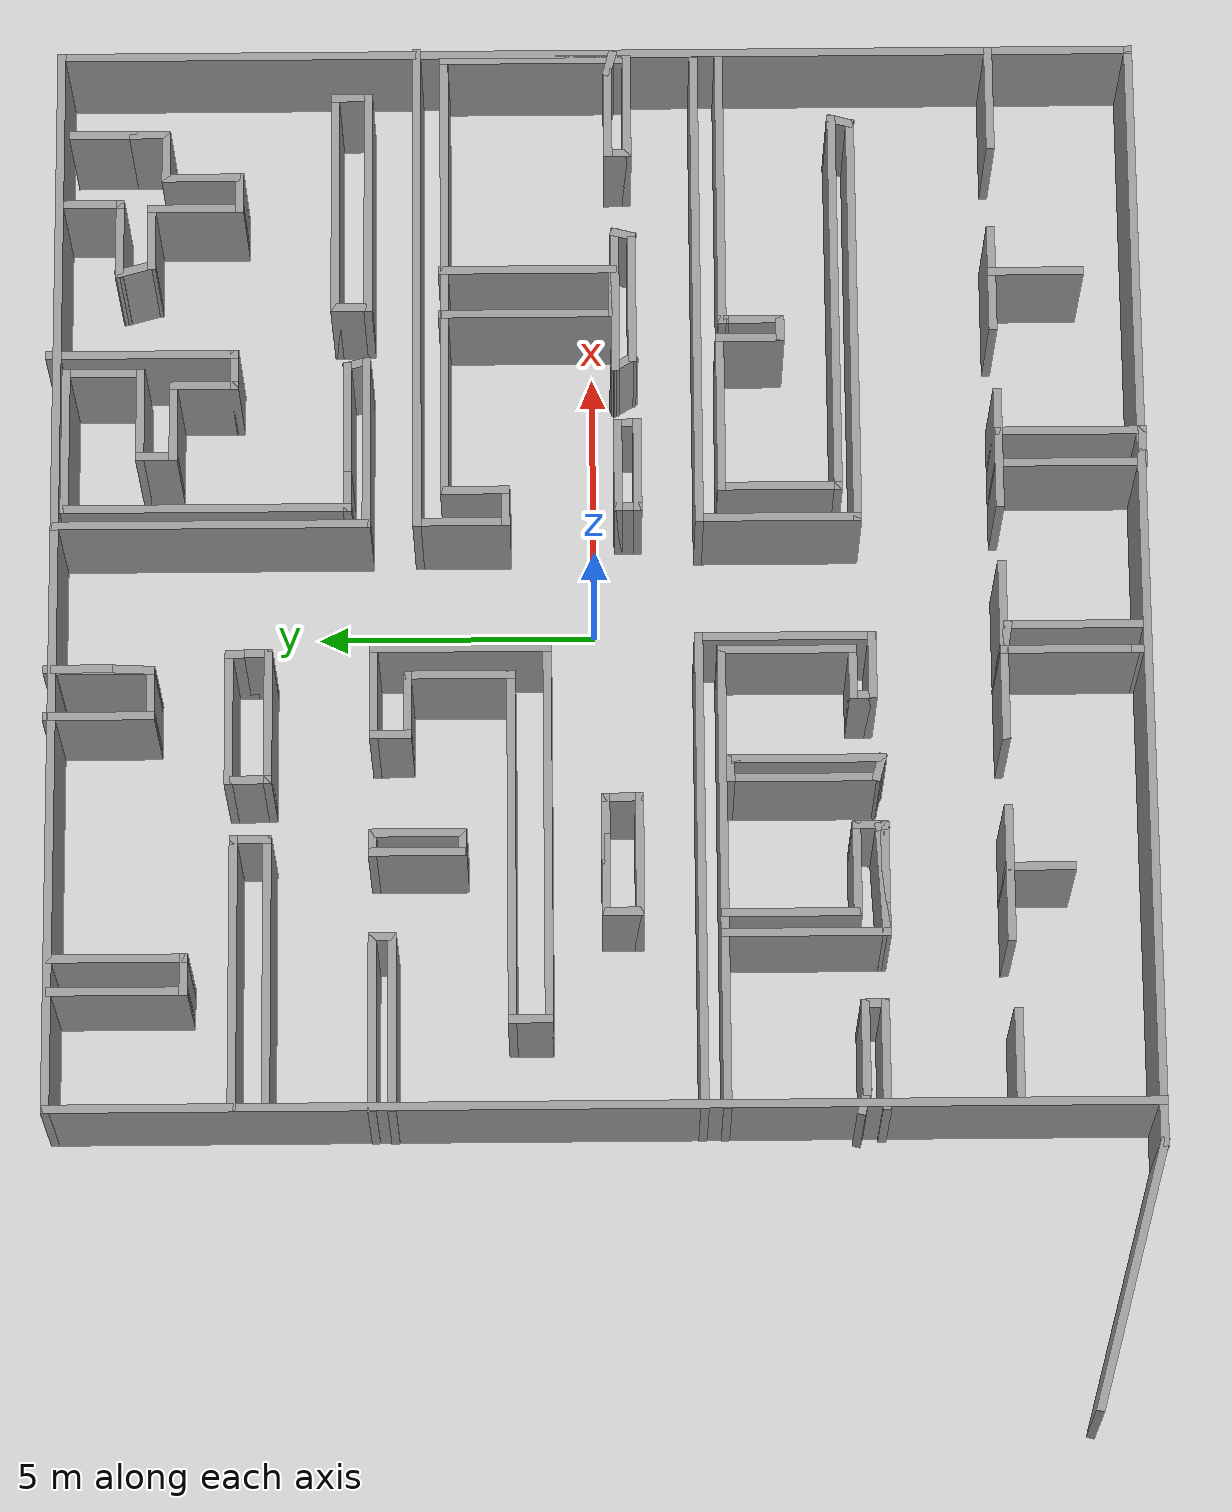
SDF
<sdf version="1.6">
 <world name="default">
  <scene><ambient>0.4 0.4 0.4 1</ambient><background>0.7 0.7 0.7 1</background><shadows>1</shadows></scene>
  <light name="sun" type="directional">
   <pose>0 0 10 0 -0 0</pose>
   <diffuse>0.8 0.8 0.8 1</diffuse>
   <specular>0.2 0.2 0.2 1</specular>
   <attenuation>
    <range>1000</range>
    <constant>0.9</constant>
    <linear>0.01</linear>
    <quadratic>0.001</quadratic>
   </attenuation>
   <direction>-0.5 0.1 -0.9</direction>
  </light>
  <model name="ground_plane">
   <static>1</static>
   <link name="link">
    <collision name="collision">
     <geometry><plane><normal>0 0 1</normal><size>100 100</size></plane></geometry>
     <surface>
      <contact><collide_bitmask>65535</collide_bitmask></contact>
      <friction><ode><mu>100</mu><mu2>50</mu2></ode></friction>
     </surface>
    </collision>
    <visual name="visual">
     <cast_shadows>0</cast_shadows>
     <geometry><plane><normal>0 0 1</normal><size>100 100</size></plane></geometry>
     <material>
      <script><uri>file://media/materials/scripts/gazebo.material</uri><name>Gazebo/Grey</name></script>
     </material>
    </visual>
   </link>
  </model>
  <physics name="default_physics" default="0" type="ode">
   <real_time_update_rate>1000</real_time_update_rate>
   <max_step_size>0.001</max_step_size>
   <real_time_factor>1</real_time_factor>
   <ode>
    <solver>
     <type>quick</type>
     <iters>150</iters>
     <precon_iters>0</precon_iters>
     <sor>1.4</sor>
     <use_dynamic_moi_rescaling>1</use_dynamic_moi_rescaling>
    </solver>
    <constraints>
     <cfm>1e-05</cfm>
     <erp>0.2</erp>
     <contact_max_correcting_vel>2000</contact_max_correcting_vel>
     <contact_surface_layer>0.01</contact_surface_layer>
    </constraints>
   </ode>
  </physics>
  <gravity>0 0 -9.8</gravity>
  <magnetic_field>6e-06 2.3e-05 -4.2e-05</magnetic_field>
  <atmosphere type="adiabatic"/>
  <audio><device>default</device></audio>
  <spherical_coordinates>
   <surface_model>EARTH_WGS84</surface_model>
   <latitude_deg>0</latitude_deg>
   <longitude_deg>0</longitude_deg>
   <elevation>0</elevation>
   <heading_deg>0</heading_deg>
  </spherical_coordinates>
  <model name="maze3">
   <pose>-2.12567 -0.040399 0 0 -0 0</pose>
   <link name="Wall_100">
    <collision name="Wall_100_Collision">
     <geometry><box><size>6.5 0.15 2.5</size></box></geometry>
     <pose>0 0 1.25 0 -0 0</pose>
    </collision>
    <visual name="Wall_100_Visual">
     <pose>0 0 1.25 0 -0 0</pose>
     <geometry><box><size>6.5 0.15 2.5</size></box></geometry>
     <material>
      <script><uri>file://media/materials/scripts/gazebo.material</uri><name>Gazebo/Grey</name></script>
      <ambient>1 1 1 1</ambient>
     </material>
     <meta><layer>0</layer></meta>
    </visual>
    <pose>-2.484 1.54922 0 0 -0 3.14159</pose>
   </link>
   <link name="Wall_101">
    <collision name="Wall_101_Collision">
     <geometry><box><size>0.8 0.15 2.5</size></box></geometry>
     <pose>0 0 1.25 0 -0 0</pose>
    </collision>
    <visual name="Wall_101_Visual">
     <pose>0 0 1.25 0 -0 0</pose>
     <geometry><box><size>0.8 0.15 2.5</size></box></geometry>
     <material>
      <script><uri>file://media/materials/scripts/gazebo.material</uri><name>Gazebo/Grey</name></script>
      <ambient>1 1 1 1</ambient>
     </material>
     <meta><layer>0</layer></meta>
    </visual>
    <pose>-5.659 1.22422 0 0 -0 -1.5708</pose>
   </link>
   <link name="Wall_103">
    <collision name="Wall_103_Collision">
     <geometry><box><size>3.25 0.15 2.5</size></box></geometry>
     <pose>0 0 1.25 0 -0 0</pose>
    </collision>
    <visual name="Wall_103_Visual">
     <pose>0 0 1.25 0 -0 0</pose>
     <geometry><box><size>3.25 0.15 2.5</size></box></geometry>
     <material>
      <script><uri>file://media/materials/scripts/gazebo.material</uri><name>Gazebo/Grey</name></script>
      <ambient>1 1 1 1</ambient>
     </material>
     <meta><layer>0</layer></meta>
    </visual>
    <pose>-5.69081 4.01632 0 0 -0 0</pose>
   </link>
   <link name="Wall_104">
    <collision name="Wall_104_Collision">
     <geometry><box><size>0.5 0.15 2.5</size></box></geometry>
     <pose>0 0 1.25 0 -0 0</pose>
    </collision>
    <visual name="Wall_104_Visual">
     <pose>0 0 1.25 0 -0 0</pose>
     <geometry><box><size>0.5 0.15 2.5</size></box></geometry>
     <material>
      <script><uri>file://media/materials/scripts/gazebo.material</uri><name>Gazebo/Grey</name></script>
      <ambient>1 1 1 1</ambient>
     </material>
     <meta><layer>0</layer></meta>
    </visual>
    <pose>-4.14081 3.84132 0 0 -0 -1.5708</pose>
   </link>
   <link name="Wall_105">
    <collision name="Wall_105_Collision">
     <geometry><box><size>3.25 0.15 2.5</size></box></geometry>
     <pose>0 0 1.25 0 -0 0</pose>
    </collision>
    <visual name="Wall_105_Visual">
     <pose>0 0 1.25 0 -0 0</pose>
     <geometry><box><size>3.25 0.15 2.5</size></box></geometry>
     <material>
      <script><uri>file://media/materials/scripts/gazebo.material</uri><name>Gazebo/Grey</name></script>
      <ambient>1 1 1 1</ambient>
     </material>
     <meta><layer>0</layer></meta>
    </visual>
    <pose>-5.69081 3.66632 0 0 -0 3.14159</pose>
   </link>
   <link name="Wall_107">
    <collision name="Wall_107_Collision">
     <geometry><box><size>1.75 0.15 2.5</size></box></geometry>
     <pose>0 0 1.25 0 -0 0</pose>
    </collision>
    <visual name="Wall_107_Visual">
     <pose>0 0 1.25 0 -0 0</pose>
     <geometry><box><size>1.75 0.15 2.5</size></box></geometry>
     <material>
      <script><uri>file://media/materials/scripts/gazebo.material</uri><name>Gazebo/Grey</name></script>
      <ambient>1 1 1 1</ambient>
     </material>
     <meta><layer>0</layer></meta>
    </visual>
    <pose>-2.58842 3.21632 0 0 -0 -1.5708</pose>
   </link>
   <link name="Wall_108">
    <collision name="Wall_108_Collision">
     <geometry><box><size>0.5 0.15 2.5</size></box></geometry>
     <pose>0 0 1.25 0 -0 0</pose>
    </collision>
    <visual name="Wall_108_Visual">
     <pose>0 0 1.25 0 -0 0</pose>
     <geometry><box><size>0.5 0.15 2.5</size></box></geometry>
     <material>
      <script><uri>file://media/materials/scripts/gazebo.material</uri><name>Gazebo/Grey</name></script>
      <ambient>1 1 1 1</ambient>
     </material>
     <meta><layer>0</layer></meta>
    </visual>
    <pose>-2.41342 2.41632 0 0 -0 0</pose>
   </link>
   <link name="Wall_109">
    <collision name="Wall_109_Collision">
     <geometry><box><size>1.75 0.15 2.5</size></box></geometry>
     <pose>0 0 1.25 0 -0 0</pose>
    </collision>
    <visual name="Wall_109_Visual">
     <pose>0 0 1.25 0 -0 0</pose>
     <geometry><box><size>1.75 0.15 2.5</size></box></geometry>
     <material>
      <script><uri>file://media/materials/scripts/gazebo.material</uri><name>Gazebo/Grey</name></script>
      <ambient>1 1 1 1</ambient>
     </material>
     <meta><layer>0</layer></meta>
    </visual>
    <pose>-2.23842 3.21632 0 0 -0 1.5708</pose>
   </link>
   <link name="Wall_11">
    <collision name="Wall_11_Collision">
     <geometry><box><size>5 0.15 2.5</size></box></geometry>
     <pose>0 0 1.25 0 -0 0</pose>
    </collision>
    <visual name="Wall_11_Visual">
     <pose>0 0 1.25 0 -0 0</pose>
     <geometry><box><size>5 0.15 2.5</size></box></geometry>
     <material>
      <script><uri>file://media/materials/scripts/gazebo.material</uri><name>Gazebo/Grey</name></script>
      <ambient>1 1 1 1</ambient>
     </material>
     <meta><layer>0</layer></meta>
    </visual>
    <pose>-10.3122 -9.22367 0 0 -0 -0.261799</pose>
   </link>
   <link name="Wall_110">
    <collision name="Wall_110_Collision">
     <geometry><box><size>0.5 0.15 2.5</size></box></geometry>
     <pose>0 0 1.25 0 -0 0</pose>
    </collision>
    <visual name="Wall_110_Visual">
     <pose>0 0 1.25 0 -0 0</pose>
     <geometry><box><size>0.5 0.15 2.5</size></box></geometry>
     <material>
      <script><uri>file://media/materials/scripts/gazebo.material</uri><name>Gazebo/Grey</name></script>
      <ambient>1 1 1 1</ambient>
     </material>
     <meta><layer>0</layer></meta>
    </visual>
    <pose>-2.41342 4.01632 0 0 -0 3.14159</pose>
   </link>
   <link name="Wall_112">
    <collision name="Wall_112_Collision">
     <geometry><box><size>5 0.15 2.5</size></box></geometry>
     <pose>0 0 1.25 0 -0 0</pose>
    </collision>
    <visual name="Wall_112_Visual">
     <pose>0 0 1.25 0 -0 0</pose>
     <geometry><box><size>5 0.15 2.5</size></box></geometry>
     <material>
      <script><uri>file://media/materials/scripts/gazebo.material</uri><name>Gazebo/Grey</name></script>
      <ambient>1 1 1 1</ambient>
     </material>
     <meta><layer>0</layer></meta>
    </visual>
    <pose>-4.76928 6.48209 0 0 -0 0</pose>
   </link>
   <link name="Wall_113">
    <collision name="Wall_113_Collision">
     <geometry><box><size>0.75 0.15 2.5</size></box></geometry>
     <pose>0 0 1.25 0 -0 0</pose>
    </collision>
    <visual name="Wall_113_Visual">
     <pose>0 0 1.25 0 -0 0</pose>
     <geometry><box><size>0.75 0.15 2.5</size></box></geometry>
     <material>
      <script><uri>file://media/materials/scripts/gazebo.material</uri><name>Gazebo/Grey</name></script>
      <ambient>1 1 1 1</ambient>
     </material>
     <meta><layer>0</layer></meta>
    </visual>
    <pose>-2.34429 6.18209 0 0 -0 -1.5708</pose>
   </link>
   <link name="Wall_114">
    <collision name="Wall_114_Collision">
     <geometry><box><size>5 0.15 2.5</size></box></geometry>
     <pose>0 0 1.25 0 -0 0</pose>
    </collision>
    <visual name="Wall_114_Visual">
     <pose>0 0 1.25 0 -0 0</pose>
     <geometry><box><size>5 0.15 2.5</size></box></geometry>
     <material>
      <script><uri>file://media/materials/scripts/gazebo.material</uri><name>Gazebo/Grey</name></script>
      <ambient>1 1 1 1</ambient>
     </material>
     <meta><layer>0</layer></meta>
    </visual>
    <pose>-4.76928 5.88209 0 0 -0 3.14159</pose>
   </link>
   <link name="Wall_116">
    <collision name="Wall_116_Collision">
     <geometry><box><size>0.75 0.15 2.5</size></box></geometry>
     <pose>0 0 1.25 0 -0 0</pose>
    </collision>
    <visual name="Wall_116_Visual">
     <pose>0 0 1.25 0 -0 0</pose>
     <geometry><box><size>0.75 0.15 2.5</size></box></geometry>
     <material>
      <script><uri>file://media/materials/scripts/gazebo.material</uri><name>Gazebo/Grey</name></script>
      <ambient>1 1 1 1</ambient>
     </material>
     <meta><layer>0</layer></meta>
    </visual>
    <pose>-1.23922 6.18209 0 0 -0 -1.5708</pose>
   </link>
   <link name="Wall_117">
    <collision name="Wall_117_Collision">
     <geometry><box><size>2.5 0.15 2.5</size></box></geometry>
     <pose>0 0 1.25 0 -0 0</pose>
    </collision>
    <visual name="Wall_117_Visual">
     <pose>0 0 1.25 0 -0 0</pose>
     <geometry><box><size>2.5 0.15 2.5</size></box></geometry>
     <material>
      <script><uri>file://media/materials/scripts/gazebo.material</uri><name>Gazebo/Grey</name></script>
      <ambient>1 1 1 1</ambient>
     </material>
     <meta><layer>0</layer></meta>
    </visual>
    <pose>-0.064224 5.88209 0 0 -0 0</pose>
   </link>
   <link name="Wall_118">
    <collision name="Wall_118_Collision">
     <geometry><box><size>0.5 0.15 2.5</size></box></geometry>
     <pose>0 0 1.25 0 -0 0</pose>
    </collision>
    <visual name="Wall_118_Visual">
     <pose>0 0 1.25 0 -0 0</pose>
     <geometry><box><size>0.5 0.15 2.5</size></box></geometry>
     <material>
      <script><uri>file://media/materials/scripts/gazebo.material</uri><name>Gazebo/Grey</name></script>
      <ambient>1 1 1 1</ambient>
     </material>
     <meta><layer>0</layer></meta>
    </visual>
    <pose>1.11078 6.05709 0 0 -0 1.5708</pose>
   </link>
   <link name="Wall_119">
    <collision name="Wall_119_Collision">
     <geometry><box><size>0.5 0.15 2.5</size></box></geometry>
     <pose>0 0 1.25 0 -0 0</pose>
    </collision>
    <visual name="Wall_119_Visual">
     <pose>0 0 1.25 0 -0 0</pose>
     <geometry><box><size>0.5 0.15 2.5</size></box></geometry>
     <material>
      <script><uri>file://media/materials/scripts/gazebo.material</uri><name>Gazebo/Grey</name></script>
      <ambient>1 1 1 1</ambient>
     </material>
     <meta><layer>0</layer></meta>
    </visual>
    <pose>1.11078 6.40709 0 0 -0 1.5708</pose>
   </link>
   <link name="Wall_12">
    <collision name="Wall_12_Collision">
     <geometry><box><size>20.75 0.15 2.5</size></box></geometry>
     <pose>0 0 1.25 0 -0 0</pose>
    </collision>
    <visual name="Wall_12_Visual">
     <pose>0 0 1.25 0 -0 0</pose>
     <geometry><box><size>20.75 0.15 2.5</size></box></geometry>
     <material>
      <script><uri>file://media/materials/scripts/gazebo.material</uri><name>Gazebo/Grey</name></script>
      <ambient>1 1 1 1</ambient>
     </material>
     <meta><layer>0</layer></meta>
    </visual>
    <pose>2.33017 -9.8513 0 0 -0 0</pose>
   </link>
   <link name="Wall_120">
    <collision name="Wall_120_Collision">
     <geometry><box><size>2.5 0.15 2.5</size></box></geometry>
     <pose>0 0 1.25 0 -0 0</pose>
    </collision>
    <visual name="Wall_120_Visual">
     <pose>0 0 1.25 0 -0 0</pose>
     <geometry><box><size>2.5 0.15 2.5</size></box></geometry>
     <material>
      <script><uri>file://media/materials/scripts/gazebo.material</uri><name>Gazebo/Grey</name></script>
      <ambient>1 1 1 1</ambient>
     </material>
     <meta><layer>0</layer></meta>
    </visual>
    <pose>-0.064224 6.58209 0 0 -0 3.14159</pose>
   </link>
   <link name="Wall_122">
    <collision name="Wall_122_Collision">
     <geometry><box><size>2 0.15 2.5</size></box></geometry>
     <pose>0 0 1.25 0 -0 0</pose>
    </collision>
    <visual name="Wall_122_Visual">
     <pose>0 0 1.25 0 -0 0</pose>
     <geometry><box><size>2 0.15 2.5</size></box></geometry>
     <material>
      <script><uri>file://media/materials/scripts/gazebo.material</uri><name>Gazebo/Grey</name></script>
      <ambient>1 1 1 1</ambient>
     </material>
     <meta><layer>0</layer></meta>
    </visual>
    <pose>-0.029602 8.90681 0 0 -0 -1.5708</pose>
   </link>
   <link name="Wall_123">
    <collision name="Wall_123_Collision">
     <geometry><box><size>1 0.15 2.5</size></box></geometry>
     <pose>0 0 1.25 0 -0 0</pose>
    </collision>
    <visual name="Wall_123_Visual">
     <pose>0 0 1.25 0 -0 0</pose>
     <geometry><box><size>1 0.15 2.5</size></box></geometry>
     <material>
      <script><uri>file://media/materials/scripts/gazebo.material</uri><name>Gazebo/Grey</name></script>
      <ambient>1 1 1 1</ambient>
     </material>
     <meta><layer>0</layer></meta>
    </visual>
    <pose>0.395398 7.98181 0 0 -0 0</pose>
   </link>
   <link name="Wall_124">
    <collision name="Wall_124_Collision">
     <geometry><box><size>1.75 0.15 2.5</size></box></geometry>
     <pose>0 0 1.25 0 -0 0</pose>
    </collision>
    <visual name="Wall_124_Visual">
     <pose>0 0 1.25 0 -0 0</pose>
     <geometry><box><size>1.75 0.15 2.5</size></box></geometry>
     <material>
      <script><uri>file://media/materials/scripts/gazebo.material</uri><name>Gazebo/Grey</name></script>
      <ambient>1 1 1 1</ambient>
     </material>
     <meta><layer>0</layer></meta>
    </visual>
    <pose>0.820398 8.78181 0 0 -0 1.5708</pose>
   </link>
   <link name="Wall_126">
    <collision name="Wall_126_Collision">
     <geometry><box><size>1.25 0.15 2.5</size></box></geometry>
     <pose>0 0 1.25 0 -0 0</pose>
    </collision>
    <visual name="Wall_126_Visual">
     <pose>0 0 1.25 0 -0 0</pose>
     <geometry><box><size>1.25 0.15 2.5</size></box></geometry>
     <material>
      <script><uri>file://media/materials/scripts/gazebo.material</uri><name>Gazebo/Grey</name></script>
      <ambient>1 1 1 1</ambient>
     </material>
     <meta><layer>0</layer></meta>
    </visual>
    <pose>0.854352 9.28181 0 0 -0 -1.5708</pose>
   </link>
   <link name="Wall_127">
    <collision name="Wall_127_Collision">
     <geometry><box><size>0.900768 0.15 2.5</size></box></geometry>
     <pose>0 0 1.25 0 -0 0</pose>
    </collision>
    <visual name="Wall_127_Visual">
     <pose>0 0 1.25 0 -0 0</pose>
     <geometry><box><size>0.900768 0.15 2.5</size></box></geometry>
     <material>
      <script><uri>file://media/materials/scripts/gazebo.material</uri><name>Gazebo/Grey</name></script>
      <ambient>1 1 1 1</ambient>
     </material>
     <meta><layer>0</layer></meta>
    </visual>
    <pose>0.837375 8.35681 0 0 -0 -1.61604</pose>
   </link>
   <link name="Wall_129">
    <collision name="Wall_129_Collision">
     <geometry><box><size>2.5 0.15 2.5</size></box></geometry>
     <pose>0 0 1.25 0 -0 0</pose>
    </collision>
    <visual name="Wall_129_Visual">
     <pose>0 0 1.25 0 -0 0</pose>
     <geometry><box><size>2.5 0.15 2.5</size></box></geometry>
     <material>
      <script><uri>file://media/materials/scripts/gazebo.material</uri><name>Gazebo/Grey</name></script>
      <ambient>1 1 1 1</ambient>
     </material>
     <meta><layer>0</layer></meta>
    </visual>
    <pose>-5.10071 8.51724 0 0 -0 -1.5708</pose>
   </link>
   <link name="Wall_13">
    <collision name="Wall_13_Collision">
     <geometry><box><size>19.75 0.15 2.5</size></box></geometry>
     <pose>0 0 1.25 0 -0 0</pose>
    </collision>
    <visual name="Wall_13_Visual">
     <pose>0 0 1.25 0 -0 0</pose>
     <geometry><box><size>19.75 0.15 2.5</size></box></geometry>
     <material>
      <script><uri>file://media/materials/scripts/gazebo.material</uri><name>Gazebo/Grey</name></script>
      <ambient>1 1 1 1</ambient>
     </material>
     <meta><layer>0</layer></meta>
    </visual>
    <pose>12.6302 -0.051301 0 0 -0 1.5708</pose>
   </link>
   <link name="Wall_130">
    <collision name="Wall_130_Collision">
     <geometry><box><size>0.75 0.15 2.5</size></box></geometry>
     <pose>0 0 1.25 0 -0 0</pose>
    </collision>
    <visual name="Wall_130_Visual">
     <pose>0 0 1.25 0 -0 0</pose>
     <geometry><box><size>0.75 0.15 2.5</size></box></geometry>
     <material>
      <script><uri>file://media/materials/scripts/gazebo.material</uri><name>Gazebo/Grey</name></script>
      <ambient>1 1 1 1</ambient>
     </material>
     <meta><layer>0</layer></meta>
    </visual>
    <pose>-4.80071 7.34224 0 0 -0 0</pose>
   </link>
   <link name="Wall_131">
    <collision name="Wall_131_Collision">
     <geometry><box><size>2.5 0.15 2.5</size></box></geometry>
     <pose>0 0 1.25 0 -0 0</pose>
    </collision>
    <visual name="Wall_131_Visual">
     <pose>0 0 1.25 0 -0 0</pose>
     <geometry><box><size>2.5 0.15 2.5</size></box></geometry>
     <material>
      <script><uri>file://media/materials/scripts/gazebo.material</uri><name>Gazebo/Grey</name></script>
      <ambient>1 1 1 1</ambient>
     </material>
     <meta><layer>0</layer></meta>
    </visual>
    <pose>-4.50071 8.51724 0 0 -0 1.5708</pose>
   </link>
   <link name="Wall_133">
    <collision name="Wall_133_Collision">
     <geometry><box><size>5.75 0.15 2.5</size></box></geometry>
     <pose>0 0 1.25 0 -0 0</pose>
    </collision>
    <visual name="Wall_133_Visual">
     <pose>0 0 1.25 0 -0 0</pose>
     <geometry><box><size>5.75 0.15 2.5</size></box></geometry>
     <material>
      <script><uri>file://media/materials/scripts/gazebo.material</uri><name>Gazebo/Grey</name></script>
      <ambient>1 1 1 1</ambient>
     </material>
     <meta><layer>0</layer></meta>
    </visual>
    <pose>3.55274 6.93876 0 0 -0 -1.5708</pose>
   </link>
   <link name="Wall_134">
    <collision name="Wall_134_Collision">
     <geometry><box><size>3.25 0.15 2.5</size></box></geometry>
     <pose>0 0 1.25 0 -0 0</pose>
    </collision>
    <visual name="Wall_134_Visual">
     <pose>0 0 1.25 0 -0 0</pose>
     <geometry><box><size>3.25 0.15 2.5</size></box></geometry>
     <material>
      <script><uri>file://media/materials/scripts/gazebo.material</uri><name>Gazebo/Grey</name></script>
      <ambient>1 1 1 1</ambient>
     </material>
     <meta><layer>0</layer></meta>
    </visual>
    <pose>5.10274 4.13876 0 0 -0 0</pose>
   </link>
   <link name="Wall_135">
    <collision name="Wall_135_Collision">
     <geometry><box><size>0.5 0.15 2.5</size></box></geometry>
     <pose>0 0 1.25 0 -0 0</pose>
    </collision>
    <visual name="Wall_135_Visual">
     <pose>0 0 1.25 0 -0 0</pose>
     <geometry><box><size>0.5 0.15 2.5</size></box></geometry>
     <material>
      <script><uri>file://media/materials/scripts/gazebo.material</uri><name>Gazebo/Grey</name></script>
      <ambient>1 1 1 1</ambient>
     </material>
     <meta><layer>0</layer></meta>
    </visual>
    <pose>6.60745 4.3078 0 0 -0 1.8326</pose>
   </link>
   <link name="Wall_136">
    <collision name="Wall_136_Collision">
     <geometry><box><size>2.25 0.15 2.5</size></box></geometry>
     <pose>0 0 1.25 0 -0 0</pose>
    </collision>
    <visual name="Wall_136_Visual">
     <pose>0 0 1.25 0 -0 0</pose>
     <geometry><box><size>2.25 0.15 2.5</size></box></geometry>
     <material>
      <script><uri>file://media/materials/scripts/gazebo.material</uri><name>Gazebo/Grey</name></script>
      <ambient>1 1 1 1</ambient>
     </material>
     <meta><layer>0</layer></meta>
    </visual>
    <pose>5.51215 4.47684 0 0 -0 3.14159</pose>
   </link>
   <link name="Wall_137">
    <collision name="Wall_137_Collision">
     <geometry><box><size>0.75 0.15 2.5</size></box></geometry>
     <pose>0 0 1.25 0 -0 0</pose>
    </collision>
    <visual name="Wall_137_Visual">
     <pose>0 0 1.25 0 -0 0</pose>
     <geometry><box><size>0.75 0.15 2.5</size></box></geometry>
     <material>
      <script><uri>file://media/materials/scripts/gazebo.material</uri><name>Gazebo/Grey</name></script>
      <ambient>1 1 1 1</ambient>
     </material>
     <meta><layer>0</layer></meta>
    </visual>
    <pose>4.16215 4.47684 0 0 -0 3.14159</pose>
   </link>
   <link name="Wall_138">
    <collision name="Wall_138_Collision">
     <geometry><box><size>5.25 0.15 2.5</size></box></geometry>
     <pose>0 0 1.25 0 -0 0</pose>
    </collision>
    <visual name="Wall_138_Visual">
     <pose>0 0 1.25 0 -0 0</pose>
     <geometry><box><size>5.25 0.15 2.5</size></box></geometry>
     <material>
      <script><uri>file://media/materials/scripts/gazebo.material</uri><name>Gazebo/Grey</name></script>
      <ambient>1 1 1 1</ambient>
     </material>
     <meta><layer>0</layer></meta>
    </visual>
    <pose>3.86215 7.02684 0 0 -0 1.5708</pose>
   </link>
   <link name="Wall_139">
    <collision name="Wall_139_Collision">
     <geometry><box><size>2.75 0.15 2.5</size></box></geometry>
     <pose>0 0 1.25 0 -0 0</pose>
    </collision>
    <visual name="Wall_139_Visual">
     <pose>0 0 1.25 0 -0 0</pose>
     <geometry><box><size>2.75 0.15 2.5</size></box></geometry>
     <material>
      <script><uri>file://media/materials/scripts/gazebo.material</uri><name>Gazebo/Grey</name></script>
      <ambient>1 1 1 1</ambient>
     </material>
     <meta><layer>0</layer></meta>
    </visual>
    <pose>5.16215 9.57684 0 0 -0 0</pose>
   </link>
   <link name="Wall_14">
    <collision name="Wall_14_Collision">
     <geometry><box><size>20 0.15 2.5</size></box></geometry>
     <pose>0 0 1.25 0 -0 0</pose>
    </collision>
    <visual name="Wall_14_Visual">
     <pose>0 0 1.25 0 -0 0</pose>
     <geometry><box><size>20 0.15 2.5</size></box></geometry>
     <material>
      <script><uri>file://media/materials/scripts/gazebo.material</uri><name>Gazebo/Grey</name></script>
      <ambient>1 1 1 1</ambient>
     </material>
     <meta><layer>0</layer></meta>
    </visual>
    <pose>2.70517 9.7487 0 0 -0 3.14159</pose>
   </link>
   <link name="Wall_140">
    <collision name="Wall_140_Collision">
     <geometry><box><size>1.5 0.15 2.5</size></box></geometry>
     <pose>0 0 1.25 0 -0 0</pose>
    </collision>
    <visual name="Wall_140_Visual">
     <pose>0 0 1.25 0 -0 0</pose>
     <geometry><box><size>1.5 0.15 2.5</size></box></geometry>
     <material>
      <script><uri>file://media/materials/scripts/gazebo.material</uri><name>Gazebo/Grey</name></script>
      <ambient>1 1 1 1</ambient>
     </material>
     <meta><layer>0</layer></meta>
    </visual>
    <pose>6.46215 8.90184 0 0 -0 -1.5708</pose>
   </link>
   <link name="Wall_141">
    <collision name="Wall_141_Collision">
     <geometry><box><size>1.75 0.15 2.5</size></box></geometry>
     <pose>0 0 1.25 0 -0 0</pose>
    </collision>
    <visual name="Wall_141_Visual">
     <pose>0 0 1.25 0 -0 0</pose>
     <geometry><box><size>1.75 0.15 2.5</size></box></geometry>
     <material>
      <script><uri>file://media/materials/scripts/gazebo.material</uri><name>Gazebo/Grey</name></script>
      <ambient>1 1 1 1</ambient>
     </material>
     <meta><layer>0</layer></meta>
    </visual>
    <pose>5.66215 8.22683 0 0 -0 3.14159</pose>
   </link>
   <link name="Wall_142">
    <collision name="Wall_142_Collision">
     <geometry><box><size>0.75 0.15 2.5</size></box></geometry>
     <pose>0 0 1.25 0 -0 0</pose>
    </collision>
    <visual name="Wall_142_Visual">
     <pose>0 0 1.25 0 -0 0</pose>
     <geometry><box><size>0.75 0.15 2.5</size></box></geometry>
     <material>
      <script><uri>file://media/materials/scripts/gazebo.material</uri><name>Gazebo/Grey</name></script>
      <ambient>1 1 1 1</ambient>
     </material>
     <meta><layer>0</layer></meta>
    </visual>
    <pose>4.86215 7.92684 0 0 -0 -1.5708</pose>
   </link>
   <link name="Wall_143">
    <collision name="Wall_143_Collision">
     <geometry><box><size>1.5 0.15 2.5</size></box></geometry>
     <pose>0 0 1.25 0 -0 0</pose>
    </collision>
    <visual name="Wall_143_Visual">
     <pose>0 0 1.25 0 -0 0</pose>
     <geometry><box><size>1.5 0.15 2.5</size></box></geometry>
     <material>
      <script><uri>file://media/materials/scripts/gazebo.material</uri><name>Gazebo/Grey</name></script>
      <ambient>1 1 1 1</ambient>
     </material>
     <meta><layer>0</layer></meta>
    </visual>
    <pose>5.53715 7.62684 0 0 -0 0</pose>
   </link>
   <link name="Wall_144">
    <collision name="Wall_144_Collision">
     <geometry><box><size>1.25 0.15 2.5</size></box></geometry>
     <pose>0 0 1.25 0 -0 0</pose>
    </collision>
    <visual name="Wall_144_Visual">
     <pose>0 0 1.25 0 -0 0</pose>
     <geometry><box><size>1.25 0.15 2.5</size></box></geometry>
     <material>
      <script><uri>file://media/materials/scripts/gazebo.material</uri><name>Gazebo/Grey</name></script>
      <ambient>1 1 1 1</ambient>
     </material>
     <meta><layer>0</layer></meta>
    </visual>
    <pose>6.21215 7.07684 0 0 -0 -1.5708</pose>
   </link>
   <link name="Wall_145">
    <collision name="Wall_145_Collision">
     <geometry><box><size>0.75 0.15 2.5</size></box></geometry>
     <pose>0 0 1.25 0 -0 0</pose>
    </collision>
    <visual name="Wall_145_Visual">
     <pose>0 0 1.25 0 -0 0</pose>
     <geometry><box><size>0.75 0.15 2.5</size></box></geometry>
     <material>
      <script><uri>file://media/materials/scripts/gazebo.material</uri><name>Gazebo/Grey</name></script>
      <ambient>1 1 1 1</ambient>
     </material>
     <meta><layer>0</layer></meta>
    </visual>
    <pose>6.51215 6.52684 0 0 -0 0</pose>
   </link>
   <link name="Wall_146">
    <collision name="Wall_146_Collision">
     <geometry><box><size>3.5 0.15 2.5</size></box></geometry>
     <pose>0 0 1.25 0 -0 0</pose>
    </collision>
    <visual name="Wall_146_Visual">
     <pose>0 0 1.25 0 -0 0</pose>
     <geometry><box><size>3.5 0.15 2.5</size></box></geometry>
     <material>
      <script><uri>file://media/materials/scripts/gazebo.material</uri><name>Gazebo/Grey</name></script>
      <ambient>1 1 1 1</ambient>
     </material>
     <meta><layer>0</layer></meta>
    </visual>
    <pose>6.81215 8.20184 0 0 -0 1.5708</pose>
   </link>
   <link name="Wall_148">
    <collision name="Wall_148_Collision">
     <geometry><box><size>4.25 0.15 2.5</size></box></geometry>
     <pose>0 0 1.25 0 -0 0</pose>
    </collision>
    <visual name="Wall_148_Visual">
     <pose>0 0 1.25 0 -0 0</pose>
     <geometry><box><size>4.25 0.15 2.5</size></box></geometry>
     <material>
      <script><uri>file://media/materials/scripts/gazebo.material</uri><name>Gazebo/Grey</name></script>
      <ambient>1 1 1 1</ambient>
     </material>
     <meta><layer>0</layer></meta>
    </visual>
    <pose>9.74337 4.71418 0 0 -0 0</pose>
   </link>
   <link name="Wall_149">
    <collision name="Wall_149_Collision">
     <geometry><box><size>0.75 0.15 2.5</size></box></geometry>
     <pose>0 0 1.25 0 -0 0</pose>
    </collision>
    <visual name="Wall_149_Visual">
     <pose>0 0 1.25 0 -0 0</pose>
     <geometry><box><size>0.75 0.15 2.5</size></box></geometry>
     <material>
      <script><uri>file://media/materials/scripts/gazebo.material</uri><name>Gazebo/Grey</name></script>
      <ambient>1 1 1 1</ambient>
     </material>
     <meta><layer>0</layer></meta>
    </visual>
    <pose>11.7934 4.41418 0 0 -0 -1.5708</pose>
   </link>
   <link name="Wall_15">
    <collision name="Wall_15_Collision">
     <geometry><box><size>19.75 0.15 2.5</size></box></geometry>
     <pose>0 0 1.25 0 -0 0</pose>
    </collision>
    <visual name="Wall_15_Visual">
     <pose>0 0 1.25 0 -0 0</pose>
     <geometry><box><size>19.75 0.15 2.5</size></box></geometry>
     <material>
      <script><uri>file://media/materials/scripts/gazebo.material</uri><name>Gazebo/Grey</name></script>
      <ambient>1 1 1 1</ambient>
     </material>
     <meta><layer>0</layer></meta>
    </visual>
    <pose>-7.21983 -0.051301 0 0 -0 -1.5708</pose>
   </link>
   <link name="Wall_150">
    <collision name="Wall_150_Collision">
     <geometry><box><size>4.25 0.15 2.5</size></box></geometry>
     <pose>0 0 1.25 0 -0 0</pose>
    </collision>
    <visual name="Wall_150_Visual">
     <pose>0 0 1.25 0 -0 0</pose>
     <geometry><box><size>4.25 0.15 2.5</size></box></geometry>
     <material>
      <script><uri>file://media/materials/scripts/gazebo.material</uri><name>Gazebo/Grey</name></script>
      <ambient>1 1 1 1</ambient>
     </material>
     <meta><layer>0</layer></meta>
    </visual>
    <pose>9.74337 4.11418 0 0 -0 3.14159</pose>
   </link>
   <link name="Wall_151">
    <collision name="Wall_151_Collision">
     <geometry><box><size>0.75 0.15 2.5</size></box></geometry>
     <pose>0 0 1.25 0 -0 0</pose>
    </collision>
    <visual name="Wall_151_Visual">
     <pose>0 0 1.25 0 -0 0</pose>
     <geometry><box><size>0.75 0.15 2.5</size></box></geometry>
     <material>
      <script><uri>file://media/materials/scripts/gazebo.material</uri><name>Gazebo/Grey</name></script>
      <ambient>1 1 1 1</ambient>
     </material>
     <meta><layer>0</layer></meta>
    </visual>
    <pose>7.69337 4.41418 0 0 -0 1.5708</pose>
   </link>
   <link name="Wall_153">
    <collision name="Wall_153_Collision">
     <geometry><box><size>1.25 0.15 2.5</size></box></geometry>
     <pose>0 0 1.25 0 -0 0</pose>
    </collision>
    <visual name="Wall_153_Visual">
     <pose>0 0 1.25 0 -0 0</pose>
     <geometry><box><size>1.25 0.15 2.5</size></box></geometry>
     <material>
      <script><uri>file://media/materials/scripts/gazebo.material</uri><name>Gazebo/Grey</name></script>
      <ambient>1 1 1 1</ambient>
     </material>
     <meta><layer>0</layer></meta>
    </visual>
    <pose>9.74042 9.18876 0 0 -0 -1.5708</pose>
   </link>
   <link name="Wall_154">
    <collision name="Wall_154_Collision">
     <geometry><box><size>1.5 0.15 2.5</size></box></geometry>
     <pose>0 0 1.25 0 -0 0</pose>
    </collision>
    <visual name="Wall_154_Visual">
     <pose>0 0 1.25 0 -0 0</pose>
     <geometry><box><size>1.5 0.15 2.5</size></box></geometry>
     <material>
      <script><uri>file://media/materials/scripts/gazebo.material</uri><name>Gazebo/Grey</name></script>
      <ambient>1 1 1 1</ambient>
     </material>
     <meta><layer>0</layer></meta>
    </visual>
    <pose>9.06542 8.63876 0 0 -0 3.14159</pose>
   </link>
   <link name="Wall_155">
    <collision name="Wall_155_Collision">
     <geometry><box><size>0.75 0.15 2.5</size></box></geometry>
     <pose>0 0 1.25 0 -0 0</pose>
    </collision>
    <visual name="Wall_155_Visual">
     <pose>0 0 1.25 0 -0 0</pose>
     <geometry><box><size>0.75 0.15 2.5</size></box></geometry>
     <material>
      <script><uri>file://media/materials/scripts/gazebo.material</uri><name>Gazebo/Grey</name></script>
      <ambient>1 1 1 1</ambient>
     </material>
     <meta><layer>0</layer></meta>
    </visual>
    <pose>8.46806 8.34898 0 0 -0 -1.309</pose>
   </link>
   <link name="Wall_156">
    <collision name="Wall_156_Collision">
     <geometry><box><size>1.25 0.15 2.5</size></box></geometry>
     <pose>0 0 1.25 0 -0 0</pose>
    </collision>
    <visual name="Wall_156_Visual">
     <pose>0 0 1.25 0 -0 0</pose>
     <geometry><box><size>1.25 0.15 2.5</size></box></geometry>
     <material>
      <script><uri>file://media/materials/scripts/gazebo.material</uri><name>Gazebo/Grey</name></script>
      <ambient>1 1 1 1</ambient>
     </material>
     <meta><layer>0</layer></meta>
    </visual>
    <pose>9.09571 8.05921 0 0 -0 0</pose>
   </link>
   <link name="Wall_157">
    <collision name="Wall_157_Collision">
     <geometry><box><size>1.75 0.15 2.5</size></box></geometry>
     <pose>0 0 1.25 0 -0 0</pose>
    </collision>
    <visual name="Wall_157_Visual">
     <pose>0 0 1.25 0 -0 0</pose>
     <geometry><box><size>1.75 0.15 2.5</size></box></geometry>
     <material>
      <script><uri>file://media/materials/scripts/gazebo.material</uri><name>Gazebo/Grey</name></script>
      <ambient>1 1 1 1</ambient>
     </material>
     <meta><layer>0</layer></meta>
    </visual>
    <pose>9.64571 7.25921 0 0 -0 -1.5708</pose>
   </link>
   <link name="Wall_158">
    <collision name="Wall_158_Collision">
     <geometry><box><size>0.75 0.15 2.5</size></box></geometry>
     <pose>0 0 1.25 0 -0 0</pose>
    </collision>
    <visual name="Wall_158_Visual">
     <pose>0 0 1.25 0 -0 0</pose>
     <geometry><box><size>0.75 0.15 2.5</size></box></geometry>
     <material>
      <script><uri>file://media/materials/scripts/gazebo.material</uri><name>Gazebo/Grey</name></script>
      <ambient>1 1 1 1</ambient>
     </material>
     <meta><layer>0</layer></meta>
    </visual>
    <pose>9.94571 6.45921 0 0 -0 0</pose>
   </link>
   <link name="Wall_159">
    <collision name="Wall_159_Collision">
     <geometry><box><size>1.5 0.15 2.5</size></box></geometry>
     <pose>0 0 1.25 0 -0 0</pose>
    </collision>
    <visual name="Wall_159_Visual">
     <pose>0 0 1.25 0 -0 0</pose>
     <geometry><box><size>1.5 0.15 2.5</size></box></geometry>
     <material>
      <script><uri>file://media/materials/scripts/gazebo.material</uri><name>Gazebo/Grey</name></script>
      <ambient>1 1 1 1</ambient>
     </material>
     <meta><layer>0</layer></meta>
    </visual>
    <pose>10.2457 7.13421 0 0 -0 1.5708</pose>
   </link>
   <link name="Wall_160">
    <collision name="Wall_160_Collision">
     <geometry><box><size>1 0.15 2.5</size></box></geometry>
     <pose>0 0 1.25 0 -0 0</pose>
    </collision>
    <visual name="Wall_160_Visual">
     <pose>0 0 1.25 0 -0 0</pose>
     <geometry><box><size>1 0.15 2.5</size></box></geometry>
     <material>
      <script><uri>file://media/materials/scripts/gazebo.material</uri><name>Gazebo/Grey</name></script>
      <ambient>1 1 1 1</ambient>
     </material>
     <meta><layer>0</layer></meta>
    </visual>
    <pose>10.6707 7.80921 0 0 -0 0</pose>
   </link>
   <link name="Wall_161">
    <collision name="Wall_161_Collision">
     <geometry><box><size>0.75 0.15 2.5</size></box></geometry>
     <pose>0 0 1.25 0 -0 0</pose>
    </collision>
    <visual name="Wall_161_Visual">
     <pose>0 0 1.25 0 -0 0</pose>
     <geometry><box><size>0.75 0.15 2.5</size></box></geometry>
     <material>
      <script><uri>file://media/materials/scripts/gazebo.material</uri><name>Gazebo/Grey</name></script>
      <ambient>1 1 1 1</ambient>
     </material>
     <meta><layer>0</layer></meta>
    </visual>
    <pose>11.0957 8.10921 0 0 -0 1.5708</pose>
   </link>
   <link name="Wall_162">
    <collision name="Wall_162_Collision">
     <geometry><box><size>1.25 0.15 2.5</size></box></geometry>
     <pose>0 0 1.25 0 -0 0</pose>
    </collision>
    <visual name="Wall_162_Visual">
     <pose>0 0 1.25 0 -0 0</pose>
     <geometry><box><size>1.25 0.15 2.5</size></box></geometry>
     <material>
      <script><uri>file://media/materials/scripts/gazebo.material</uri><name>Gazebo/Grey</name></script>
      <ambient>1 1 1 1</ambient>
     </material>
     <meta><layer>0</layer></meta>
    </visual>
    <pose>11.0957 8.95921 0 0 -0 1.5708</pose>
   </link>
   <link name="Wall_164">
    <collision name="Wall_164_Collision">
     <geometry><box><size>9.25 0.15 2.5</size></box></geometry>
     <pose>0 0 1.25 0 -0 0</pose>
    </collision>
    <visual name="Wall_164_Visual">
     <pose>0 0 1.25 0 -0 0</pose>
     <geometry><box><size>9.25 0.15 2.5</size></box></geometry>
     <material>
      <script><uri>file://media/materials/scripts/gazebo.material</uri><name>Gazebo/Grey</name></script>
      <ambient>1 1 1 1</ambient>
     </material>
     <meta><layer>0</layer></meta>
    </visual>
    <pose>8.12143 3.22541 0 0 -0 3.14159</pose>
   </link>
   <link name="Wall_165">
    <collision name="Wall_165_Collision">
     <geometry><box><size>1.75 0.15 2.5</size></box></geometry>
     <pose>0 0 1.25 0 -0 0</pose>
    </collision>
    <visual name="Wall_165_Visual">
     <pose>0 0 1.25 0 -0 0</pose>
     <geometry><box><size>1.75 0.15 2.5</size></box></geometry>
     <material>
      <script><uri>file://media/materials/scripts/gazebo.material</uri><name>Gazebo/Grey</name></script>
      <ambient>1 1 1 1</ambient>
     </material>
     <meta><layer>0</layer></meta>
    </visual>
    <pose>3.57143 2.42541 0 0 -0 -1.5708</pose>
   </link>
   <link name="Wall_166">
    <collision name="Wall_166_Collision">
     <geometry><box><size>0.75 0.15 2.5</size></box></geometry>
     <pose>0 0 1.25 0 -0 0</pose>
    </collision>
    <visual name="Wall_166_Visual">
     <pose>0 0 1.25 0 -0 0</pose>
     <geometry><box><size>0.75 0.15 2.5</size></box></geometry>
     <material>
      <script><uri>file://media/materials/scripts/gazebo.material</uri><name>Gazebo/Grey</name></script>
      <ambient>1 1 1 1</ambient>
     </material>
     <meta><layer>0</layer></meta>
    </visual>
    <pose>3.87143 1.62541 0 0 -0 0</pose>
   </link>
   <link name="Wall_167">
    <collision name="Wall_167_Collision">
     <geometry><box><size>1.25 0.15 2.5</size></box></geometry>
     <pose>0 0 1.25 0 -0 0</pose>
    </collision>
    <visual name="Wall_167_Visual">
     <pose>0 0 1.25 0 -0 0</pose>
     <geometry><box><size>1.25 0.15 2.5</size></box></geometry>
     <material>
      <script><uri>file://media/materials/scripts/gazebo.material</uri><name>Gazebo/Grey</name></script>
      <ambient>1 1 1 1</ambient>
     </material>
     <meta><layer>0</layer></meta>
    </visual>
    <pose>4.17143 2.17541 0 0 -0 1.5708</pose>
   </link>
   <link name="Wall_168">
    <collision name="Wall_168_Collision">
     <geometry><box><size>8.5 0.15 2.5</size></box></geometry>
     <pose>0 0 1.25 0 -0 0</pose>
    </collision>
    <visual name="Wall_168_Visual">
     <pose>0 0 1.25 0 -0 0</pose>
     <geometry><box><size>8.5 0.15 2.5</size></box></geometry>
     <material>
      <script><uri>file://media/materials/scripts/gazebo.material</uri><name>Gazebo/Grey</name></script>
      <ambient>1 1 1 1</ambient>
     </material>
     <meta><layer>0</layer></meta>
    </visual>
    <pose>8.34643 2.72541 0 0 -0 0</pose>
   </link>
   <link name="Wall_169">
    <collision name="Wall_169_Collision">
     <geometry><box><size>3.5 0.15 2.5</size></box></geometry>
     <pose>0 0 1.25 0 -0 0</pose>
    </collision>
    <visual name="Wall_169_Visual">
     <pose>0 0 1.25 0 -0 0</pose>
     <geometry><box><size>3.5 0.15 2.5</size></box></geometry>
     <material>
      <script><uri>file://media/materials/scripts/gazebo.material</uri><name>Gazebo/Grey</name></script>
      <ambient>1 1 1 1</ambient>
     </material>
     <meta><layer>0</layer></meta>
    </visual>
    <pose>12.5214 1.05041 0 0 -0 -1.5708</pose>
   </link>
   <link name="Wall_170">
    <collision name="Wall_170_Collision">
     <geometry><box><size>2 0.15 2.5</size></box></geometry>
     <pose>0 0 1.25 0 -0 0</pose>
    </collision>
    <visual name="Wall_170_Visual">
     <pose>0 0 1.25 0 -0 0</pose>
     <geometry><box><size>2 0.15 2.5</size></box></geometry>
     <material>
      <script><uri>file://media/materials/scripts/gazebo.material</uri><name>Gazebo/Grey</name></script>
      <ambient>1 1 1 1</ambient>
     </material>
     <meta><layer>0</layer></meta>
    </visual>
    <pose>11.5964 -0.624586 0 0 -0 3.14159</pose>
   </link>
   <link name="Wall_171">
    <collision name="Wall_171_Collision">
     <geometry><box><size>0.5 0.15 2.5</size></box></geometry>
     <pose>0 0 1.25 0 -0 0</pose>
    </collision>
    <visual name="Wall_171_Visual">
     <pose>0 0 1.25 0 -0 0</pose>
     <geometry><box><size>0.5 0.15 2.5</size></box></geometry>
     <material>
      <script><uri>file://media/materials/scripts/gazebo.material</uri><name>Gazebo/Grey</name></script>
      <ambient>1 1 1 1</ambient>
     </material>
     <meta><layer>0</layer></meta>
    </visual>
    <pose>10.6714 -0.449586 0 0 -0 1.5708</pose>
   </link>
   <link name="Wall_172">
    <collision name="Wall_172_Collision">
     <geometry><box><size>1.75 0.15 2.5</size></box></geometry>
     <pose>0 0 1.25 0 -0 0</pose>
    </collision>
    <visual name="Wall_172_Visual">
     <pose>0 0 1.25 0 -0 0</pose>
     <geometry><box><size>1.75 0.15 2.5</size></box></geometry>
     <material>
      <script><uri>file://media/materials/scripts/gazebo.material</uri><name>Gazebo/Grey</name></script>
      <ambient>1 1 1 1</ambient>
     </material>
     <meta><layer>0</layer></meta>
    </visual>
    <pose>11.4714 -0.274586 0 0 -0 0</pose>
   </link>
   <link name="Wall_173">
    <collision name="Wall_173_Collision">
     <geometry><box><size>0.5 0.15 2.5</size></box></geometry>
     <pose>0 0 1.25 0 -0 0</pose>
    </collision>
    <visual name="Wall_173_Visual">
     <pose>0 0 1.25 0 -0 0</pose>
     <geometry><box><size>0.5 0.15 2.5</size></box></geometry>
     <material>
      <script><uri>file://media/materials/scripts/gazebo.material</uri><name>Gazebo/Grey</name></script>
      <ambient>1 1 1 1</ambient>
     </material>
     <meta><layer>0</layer></meta>
    </visual>
    <pose>12.4405 -0.31988 0 0 -0 -0.261799</pose>
   </link>
   <link name="Wall_175">
    <collision name="Wall_175_Collision">
     <geometry><box><size>2.5 0.15 2.5</size></box></geometry>
     <pose>0 0 1.25 0 -0 0</pose>
    </collision>
    <visual name="Wall_175_Visual">
     <pose>0 0 1.25 0 -0 0</pose>
     <geometry><box><size>2.5 0.15 2.5</size></box></geometry>
     <material>
      <script><uri>file://media/materials/scripts/gazebo.material</uri><name>Gazebo/Grey</name></script>
      <ambient>1 1 1 1</ambient>
     </material>
     <meta><layer>0</layer></meta>
    </visual>
    <pose>7.86756 -0.682595 0 0 -0 3.14159</pose>
   </link>
   <link name="Wall_176">
    <collision name="Wall_176_Collision">
     <geometry><box><size>0.5 0.15 2.5</size></box></geometry>
     <pose>0 0 1.25 0 -0 0</pose>
    </collision>
    <visual name="Wall_176_Visual">
     <pose>0 0 1.25 0 -0 0</pose>
     <geometry><box><size>0.5 0.15 2.5</size></box></geometry>
     <material>
      <script><uri>file://media/materials/scripts/gazebo.material</uri><name>Gazebo/Grey</name></script>
      <ambient>1 1 1 1</ambient>
     </material>
     <meta><layer>0</layer></meta>
    </visual>
    <pose>6.60506 -0.531041 0 0 -0 2.0944</pose>
   </link>
   <link name="Wall_177">
    <collision name="Wall_177_Collision">
     <geometry><box><size>2.75 0.15 2.5</size></box></geometry>
     <pose>0 0 1.25 0 -0 0</pose>
    </collision>
    <visual name="Wall_177_Visual">
     <pose>0 0 1.25 0 -0 0</pose>
     <geometry><box><size>2.75 0.15 2.5</size></box></geometry>
     <material>
      <script><uri>file://media/materials/scripts/gazebo.material</uri><name>Gazebo/Grey</name></script>
      <ambient>1 1 1 1</ambient>
     </material>
     <meta><layer>0</layer></meta>
    </visual>
    <pose>7.81756 -0.379486 0 0 -0 0</pose>
   </link>
   <link name="Wall_178">
    <collision name="Wall_178_Collision">
     <geometry><box><size>0.46225 0.15 2.5</size></box></geometry>
     <pose>0 0 1.25 0 -0 0</pose>
    </collision>
    <visual name="Wall_178_Visual">
     <pose>0 0 1.25 0 -0 0</pose>
     <geometry><box><size>0.46225 0.15 2.5</size></box></geometry>
     <material>
      <script><uri>file://media/materials/scripts/gazebo.material</uri><name>Gazebo/Grey</name></script>
      <ambient>1 1 1 1</ambient>
     </material>
     <meta><layer>0</layer></meta>
    </visual>
    <pose>9.08006 -0.531041 0 0 -0 -1.81336</pose>
   </link>
   <link name="Wall_18">
    <collision name="Wall_18_Collision">
     <geometry><box><size>1.75 0.15 2.5</size></box></geometry>
     <pose>0 0 1.25 0 -0 0</pose>
    </collision>
    <visual name="Wall_18_Visual">
     <pose>0 0 1.25 0 -0 0</pose>
     <geometry><box><size>1.75 0.15 2.5</size></box></geometry>
     <material>
      <script><uri>file://media/materials/scripts/gazebo.material</uri><name>Gazebo/Grey</name></script>
      <ambient>1 1 1 1</ambient>
     </material>
     <meta><layer>0</layer></meta>
    </visual>
    <pose>-6.39284 -7.35775 0 0 -0 0</pose>
   </link>
   <link name="Wall_180">
    <collision name="Wall_180_Collision">
     <geometry><box><size>1.75 0.15 2.5</size></box></geometry>
     <pose>0 0 1.25 0 -0 0</pose>
    </collision>
    <visual name="Wall_180_Visual">
     <pose>0 0 1.25 0 -0 0</pose>
     <geometry><box><size>1.75 0.15 2.5</size></box></geometry>
     <material>
      <script><uri>file://media/materials/scripts/gazebo.material</uri><name>Gazebo/Grey</name></script>
      <ambient>1 1 1 1</ambient>
     </material>
     <meta><layer>0</layer></meta>
    </visual>
    <pose>4.63188 -0.403452 0 0 -0 0</pose>
   </link>
   <link name="Wall_181">
    <collision name="Wall_181_Collision">
     <geometry><box><size>0.5 0.15 2.5</size></box></geometry>
     <pose>0 0 1.25 0 -0 0</pose>
    </collision>
    <visual name="Wall_181_Visual">
     <pose>0 0 1.25 0 -0 0</pose>
     <geometry><box><size>0.5 0.15 2.5</size></box></geometry>
     <material>
      <script><uri>file://media/materials/scripts/gazebo.material</uri><name>Gazebo/Grey</name></script>
      <ambient>1 1 1 1</ambient>
     </material>
     <meta><layer>0</layer></meta>
    </visual>
    <pose>5.43188 -0.578452 0 0 -0 -1.5708</pose>
   </link>
   <link name="Wall_182">
    <collision name="Wall_182_Collision">
     <geometry><box><size>1.75 0.15 2.5</size></box></geometry>
     <pose>0 0 1.25 0 -0 0</pose>
    </collision>
    <visual name="Wall_182_Visual">
     <pose>0 0 1.25 0 -0 0</pose>
     <geometry><box><size>1.75 0.15 2.5</size></box></geometry>
     <material>
      <script><uri>file://media/materials/scripts/gazebo.material</uri><name>Gazebo/Grey</name></script>
      <ambient>1 1 1 1</ambient>
     </material>
     <meta><layer>0</layer></meta>
    </visual>
    <pose>4.63188 -0.753452 0 0 -0 3.14159</pose>
   </link>
   <link name="Wall_183">
    <collision name="Wall_183_Collision">
     <geometry><box><size>0.5 0.15 2.5</size></box></geometry>
     <pose>0 0 1.25 0 -0 0</pose>
    </collision>
    <visual name="Wall_183_Visual">
     <pose>0 0 1.25 0 -0 0</pose>
     <geometry><box><size>0.5 0.15 2.5</size></box></geometry>
     <material>
      <script><uri>file://media/materials/scripts/gazebo.material</uri><name>Gazebo/Grey</name></script>
      <ambient>1 1 1 1</ambient>
     </material>
     <meta><layer>0</layer></meta>
    </visual>
    <pose>3.83188 -0.578452 0 0 -0 1.5708</pose>
   </link>
   <link name="Wall_185">
    <collision name="Wall_185_Collision">
     <geometry><box><size>3.25 0.15 2.5</size></box></geometry>
     <pose>0 0 1.25 0 -0 0</pose>
    </collision>
    <visual name="Wall_185_Visual">
     <pose>0 0 1.25 0 -0 0</pose>
     <geometry><box><size>3.25 0.15 2.5</size></box></geometry>
     <material>
      <script><uri>file://media/materials/scripts/gazebo.material</uri><name>Gazebo/Grey</name></script>
      <ambient>1 1 1 1</ambient>
     </material>
     <meta><layer>0</layer></meta>
    </visual>
    <pose>7.5538 1.21017 0 0 -0 -1.5708</pose>
   </link>
   <link name="Wall_186">
    <collision name="Wall_186_Collision">
     <geometry><box><size>1 0.15 2.5</size></box></geometry>
     <pose>0 0 1.25 0 -0 0</pose>
    </collision>
    <visual name="Wall_186_Visual">
     <pose>0 0 1.25 0 -0 0</pose>
     <geometry><box><size>1 0.15 2.5</size></box></geometry>
     <material>
      <script><uri>file://media/materials/scripts/gazebo.material</uri><name>Gazebo/Grey</name></script>
      <ambient>1 1 1 1</ambient>
     </material>
     <meta><layer>0</layer></meta>
    </visual>
    <pose>7.9788 -0.339826 0 0 -0 0</pose>
   </link>
   <link name="Wall_187">
    <collision name="Wall_187_Collision">
     <geometry><box><size>3.25 0.15 2.5</size></box></geometry>
     <pose>0 0 1.25 0 -0 0</pose>
    </collision>
    <visual name="Wall_187_Visual">
     <pose>0 0 1.25 0 -0 0</pose>
     <geometry><box><size>3.25 0.15 2.5</size></box></geometry>
     <material>
      <script><uri>file://media/materials/scripts/gazebo.material</uri><name>Gazebo/Grey</name></script>
      <ambient>1 1 1 1</ambient>
     </material>
     <meta><layer>0</layer></meta>
    </visual>
    <pose>8.4038 1.21017 0 0 -0 1.5708</pose>
   </link>
   <link name="Wall_189">
    <collision name="Wall_189_Collision">
     <geometry><box><size>1.5 0.15 2.5</size></box></geometry>
     <pose>0 0 1.25 0 -0 0</pose>
    </collision>
    <visual name="Wall_189_Visual">
     <pose>0 0 1.25 0 -0 0</pose>
     <geometry><box><size>1.5 0.15 2.5</size></box></geometry>
     <material>
      <script><uri>file://media/materials/scripts/gazebo.material</uri><name>Gazebo/Grey</name></script>
      <ambient>1 1 1 1</ambient>
     </material>
     <meta><layer>0</layer></meta>
    </visual>
    <pose>-2.28561 -0.124308 0 0 -0 0</pose>
   </link>
   <link name="Wall_190">
    <collision name="Wall_190_Collision">
     <geometry><box><size>0.75 0.15 2.5</size></box></geometry>
     <pose>0 0 1.25 0 -0 0</pose>
    </collision>
    <visual name="Wall_190_Visual">
     <pose>0 0 1.25 0 -0 0</pose>
     <geometry><box><size>0.75 0.15 2.5</size></box></geometry>
     <material>
      <script><uri>file://media/materials/scripts/gazebo.material</uri><name>Gazebo/Grey</name></script>
      <ambient>1 1 1 1</ambient>
     </material>
     <meta><layer>0</layer></meta>
    </visual>
    <pose>-1.61061 -0.424308 0 0 -0 -1.5708</pose>
   </link>
   <link name="Wall_191">
    <collision name="Wall_191_Collision">
     <geometry><box><size>2.25 0.15 2.5</size></box></geometry>
     <pose>0 0 1.25 0 -0 0</pose>
    </collision>
    <visual name="Wall_191_Visual">
     <pose>0 0 1.25 0 -0 0</pose>
     <geometry><box><size>2.25 0.15 2.5</size></box></geometry>
     <material>
      <script><uri>file://media/materials/scripts/gazebo.material</uri><name>Gazebo/Grey</name></script>
      <ambient>1 1 1 1</ambient>
     </material>
     <meta><layer>0</layer></meta>
    </visual>
    <pose>-2.66061 -0.724308 0 0 -0 3.14159</pose>
   </link>
   <link name="Wall_192">
    <collision name="Wall_192_Collision">
     <geometry><box><size>0.75 0.15 2.5</size></box></geometry>
     <pose>0 0 1.25 0 -0 0</pose>
    </collision>
    <visual name="Wall_192_Visual">
     <pose>0 0 1.25 0 -0 0</pose>
     <geometry><box><size>0.75 0.15 2.5</size></box></geometry>
     <material>
      <script><uri>file://media/materials/scripts/gazebo.material</uri><name>Gazebo/Grey</name></script>
      <ambient>1 1 1 1</ambient>
     </material>
     <meta><layer>0</layer></meta>
    </visual>
    <pose>-3.71061 -0.424308 0 0 -0 1.5708</pose>
   </link>
   <link name="Wall_193">
    <collision name="Wall_193_Collision">
     <geometry><box><size>1.5 0.15 2.5</size></box></geometry>
     <pose>0 0 1.25 0 -0 0</pose>
    </collision>
    <visual name="Wall_193_Visual">
     <pose>0 0 1.25 0 -0 0</pose>
     <geometry><box><size>1.5 0.15 2.5</size></box></geometry>
     <material>
      <script><uri>file://media/materials/scripts/gazebo.material</uri><name>Gazebo/Grey</name></script>
      <ambient>1 1 1 1</ambient>
     </material>
     <meta><layer>0</layer></meta>
    </visual>
    <pose>-3.03561 -0.124308 0 0 -0 0</pose>
   </link>
   <link name="Wall_20">
    <collision name="Wall_20_Collision">
     <geometry><box><size>2.5 0.15 2.5</size></box></geometry>
     <pose>0 0 1.25 0 -0 0</pose>
    </collision>
    <visual name="Wall_20_Visual">
     <pose>0 0 1.25 0 -0 0</pose>
     <geometry><box><size>2.5 0.15 2.5</size></box></geometry>
     <material>
      <script><uri>file://media/materials/scripts/gazebo.material</uri><name>Gazebo/Grey</name></script>
      <ambient>1 1 1 1</ambient>
     </material>
     <meta><layer>0</layer></meta>
    </visual>
    <pose>-3.06458 -7.27684 0 0 -0 0</pose>
   </link>
   <link name="Wall_22">
    <collision name="Wall_22_Collision">
     <geometry><box><size>1.25 0.15 2.5</size></box></geometry>
     <pose>0 0 1.25 0 -0 0</pose>
    </collision>
    <visual name="Wall_22_Visual">
     <pose>0 0 1.25 0 -0 0</pose>
     <geometry><box><size>1.25 0.15 2.5</size></box></geometry>
     <material>
      <script><uri>file://media/materials/scripts/gazebo.material</uri><name>Gazebo/Grey</name></script>
      <ambient>1 1 1 1</ambient>
     </material>
     <meta><layer>0</layer></meta>
    </visual>
    <pose>-2.945 -7.82684 0 0 -0 -1.5708</pose>
   </link>
   <link name="Wall_24">
    <collision name="Wall_24_Collision">
     <geometry><box><size>1.75 0.15 2.5</size></box></geometry>
     <pose>0 0 1.25 0 -0 0</pose>
    </collision>
    <visual name="Wall_24_Visual">
     <pose>0 0 1.25 0 -0 0</pose>
     <geometry><box><size>1.75 0.15 2.5</size></box></geometry>
     <material>
      <script><uri>file://media/materials/scripts/gazebo.material</uri><name>Gazebo/Grey</name></script>
      <ambient>1 1 1 1</ambient>
     </material>
     <meta><layer>0</layer></meta>
    </visual>
    <pose>0.28233 -7.27684 0 0 -0 0</pose>
   </link>
   <link name="Wall_25">
    <collision name="Wall_25_Collision">
     <geometry><box><size>2.5 0.15 2.5</size></box></geometry>
     <pose>0 0 1.25 0 -0 0</pose>
    </collision>
    <visual name="Wall_25_Visual">
     <pose>0 0 1.25 0 -0 0</pose>
     <geometry><box><size>2.5 0.15 2.5</size></box></geometry>
     <material>
      <script><uri>file://media/materials/scripts/gazebo.material</uri><name>Gazebo/Grey</name></script>
      <ambient>1 1 1 1</ambient>
     </material>
     <meta><layer>0</layer></meta>
    </visual>
    <pose>1.08233 -8.45184 0 0 -0 -1.5708</pose>
   </link>
   <link name="Wall_30">
    <collision name="Wall_30_Collision">
     <geometry><box><size>2.5 0.15 2.5</size></box></geometry>
     <pose>0 0 1.25 0 -0 0</pose>
    </collision>
    <visual name="Wall_30_Visual">
     <pose>0 0 1.25 0 -0 0</pose>
     <geometry><box><size>2.5 0.15 2.5</size></box></geometry>
     <material>
      <script><uri>file://media/materials/scripts/gazebo.material</uri><name>Gazebo/Grey</name></script>
      <ambient>1 1 1 1</ambient>
     </material>
     <meta><layer>0</layer></meta>
    </visual>
    <pose>1.54557 -8.52917 0 0 -0 1.5708</pose>
   </link>
   <link name="Wall_31">
    <collision name="Wall_31_Collision">
     <geometry><box><size>0.619645 0.15 2.5</size></box></geometry>
     <pose>0 0 1.25 0 -0 0</pose>
    </collision>
    <visual name="Wall_31_Visual">
     <pose>0 0 1.25 0 -0 0</pose>
     <geometry><box><size>0.619645 0.15 2.5</size></box></geometry>
     <material>
      <script><uri>file://media/materials/scripts/gazebo.material</uri><name>Gazebo/Grey</name></script>
      <ambient>1 1 1 1</ambient>
     </material>
     <meta><layer>0</layer></meta>
    </visual>
    <pose>1.31395 -7.3155 0 0 -0 2.97617</pose>
   </link>
   <link name="Wall_32">
    <collision name="Wall_32_Collision">
     <geometry><box><size>1.75 0.15 2.5</size></box></geometry>
     <pose>0 0 1.25 0 -0 0</pose>
    </collision>
    <visual name="Wall_32_Visual">
     <pose>0 0 1.25 0 -0 0</pose>
     <geometry><box><size>1.75 0.15 2.5</size></box></geometry>
     <material>
      <script><uri>file://media/materials/scripts/gazebo.material</uri><name>Gazebo/Grey</name></script>
      <ambient>1 1 1 1</ambient>
     </material>
     <meta><layer>0</layer></meta>
    </visual>
    <pose>1.88233 -7.27684 0 0 -0 0</pose>
   </link>
   <link name="Wall_34">
    <collision name="Wall_34_Collision">
     <geometry><box><size>0.25 0.15 2.5</size></box></geometry>
     <pose>0 0 1.25 0 -0 0</pose>
    </collision>
    <visual name="Wall_34_Visual">
     <pose>0 0 1.25 0 -0 0</pose>
     <geometry><box><size>0.25 0.15 2.5</size></box></geometry>
     <material>
      <script><uri>file://media/materials/scripts/gazebo.material</uri><name>Gazebo/Grey</name></script>
      <ambient>1 1 1 1</ambient>
     </material>
     <meta><layer>0</layer></meta>
    </visual>
    <pose>1.08233 -9.67684 0 0 -0 -1.5708</pose>
   </link>
   <link name="Wall_37">
    <collision name="Wall_37_Collision">
     <geometry><box><size>2.25 0.15 2.5</size></box></geometry>
     <pose>0 0 1.25 0 -0 0</pose>
    </collision>
    <visual name="Wall_37_Visual">
     <pose>0 0 1.25 0 -0 0</pose>
     <geometry><box><size>2.25 0.15 2.5</size></box></geometry>
     <material>
      <script><uri>file://media/materials/scripts/gazebo.material</uri><name>Gazebo/Grey</name></script>
      <ambient>1 1 1 1</ambient>
     </material>
     <meta><layer>0</layer></meta>
    </visual>
    <pose>4.90153 -7.27684 0 0 -0 0</pose>
   </link>
   <link name="Wall_39">
    <collision name="Wall_39_Collision">
     <geometry><box><size>2.75 0.15 2.5</size></box></geometry>
     <pose>0 0 1.25 0 -0 0</pose>
    </collision>
    <visual name="Wall_39_Visual">
     <pose>0 0 1.25 0 -0 0</pose>
     <geometry><box><size>2.75 0.15 2.5</size></box></geometry>
     <material>
      <script><uri>file://media/materials/scripts/gazebo.material</uri><name>Gazebo/Grey</name></script>
      <ambient>1 1 1 1</ambient>
     </material>
     <meta><layer>0</layer></meta>
    </visual>
    <pose>4.62019 -8.57684 0 0 -0 -1.5708</pose>
   </link>
   <link name="Wall_40">
    <collision name="Wall_40_Collision">
     <geometry><box><size>0.75 0.15 2.5</size></box></geometry>
     <pose>0 0 1.25 0 -0 0</pose>
    </collision>
    <visual name="Wall_40_Visual">
     <pose>0 0 1.25 0 -0 0</pose>
     <geometry><box><size>0.75 0.15 2.5</size></box></geometry>
     <material>
      <script><uri>file://media/materials/scripts/gazebo.material</uri><name>Gazebo/Grey</name></script>
      <ambient>1 1 1 1</ambient>
     </material>
     <meta><layer>0</layer></meta>
    </visual>
    <pose>4.92019 -9.87684 0 0 -0 0</pose>
   </link>
   <link name="Wall_41">
    <collision name="Wall_41_Collision">
     <geometry><box><size>2.75 0.15 2.5</size></box></geometry>
     <pose>0 0 1.25 0 -0 0</pose>
    </collision>
    <visual name="Wall_41_Visual">
     <pose>0 0 1.25 0 -0 0</pose>
     <geometry><box><size>2.75 0.15 2.5</size></box></geometry>
     <material>
      <script><uri>file://media/materials/scripts/gazebo.material</uri><name>Gazebo/Grey</name></script>
      <ambient>1 1 1 1</ambient>
     </material>
     <meta><layer>0</layer></meta>
    </visual>
    <pose>5.22019 -8.57684 0 0 -0 1.5708</pose>
   </link>
   <link name="Wall_43">
    <collision name="Wall_43_Collision">
     <geometry><box><size>2 0.15 2.5</size></box></geometry>
     <pose>0 0 1.25 0 -0 0</pose>
    </collision>
    <visual name="Wall_43_Visual">
     <pose>0 0 1.25 0 -0 0</pose>
     <geometry><box><size>2 0.15 2.5</size></box></geometry>
     <material>
      <script><uri>file://media/materials/scripts/gazebo.material</uri><name>Gazebo/Grey</name></script>
      <ambient>1 1 1 1</ambient>
     </material>
     <meta><layer>0</layer></meta>
    </visual>
    <pose>8.1748 -7.23638 0 0 -0 0</pose>
   </link>
   <link name="Wall_46">
    <collision name="Wall_46_Collision">
     <geometry><box><size>1.75 0.15 2.5</size></box></geometry>
     <pose>0 0 1.25 0 -0 0</pose>
    </collision>
    <visual name="Wall_46_Visual">
     <pose>0 0 1.25 0 -0 0</pose>
     <geometry><box><size>1.75 0.15 2.5</size></box></geometry>
     <material>
      <script><uri>file://media/materials/scripts/gazebo.material</uri><name>Gazebo/Grey</name></script>
      <ambient>1 1 1 1</ambient>
     </material>
     <meta><layer>0</layer></meta>
    </visual>
    <pose>8.30165 -8.03638 0 0 -0 -1.5708</pose>
   </link>
   <link name="Wall_48">
    <collision name="Wall_48_Collision">
     <geometry><box><size>2 0.15 2.5</size></box></geometry>
     <pose>0 0 1.25 0 -0 0</pose>
    </collision>
    <visual name="Wall_48_Visual">
     <pose>0 0 1.25 0 -0 0</pose>
     <geometry><box><size>2 0.15 2.5</size></box></geometry>
     <material>
      <script><uri>file://media/materials/scripts/gazebo.material</uri><name>Gazebo/Grey</name></script>
      <ambient>1 1 1 1</ambient>
     </material>
     <meta><layer>0</layer></meta>
    </visual>
    <pose>11.6944 -7.27684 0 0 -0 0</pose>
   </link>
   <link name="Wall_51">
    <collision name="Wall_51_Collision">
     <geometry><box><size>8.75 0.15 2.5</size></box></geometry>
     <pose>0 0 1.25 0 -0 0</pose>
    </collision>
    <visual name="Wall_51_Visual">
     <pose>0 0 1.25 0 -0 0</pose>
     <geometry><box><size>8.75 0.15 2.5</size></box></geometry>
     <material>
      <script><uri>file://media/materials/scripts/gazebo.material</uri><name>Gazebo/Grey</name></script>
      <ambient>1 1 1 1</ambient>
     </material>
     <meta><layer>0</layer></meta>
    </visual>
    <pose>-2.9333 -1.81533 0 0 -0 0</pose>
   </link>
   <link name="Wall_52">
    <collision name="Wall_52_Collision">
     <geometry><box><size>3.25 0.15 2.5</size></box></geometry>
     <pose>0 0 1.25 0 -0 0</pose>
    </collision>
    <visual name="Wall_52_Visual">
     <pose>0 0 1.25 0 -0 0</pose>
     <geometry><box><size>3.25 0.15 2.5</size></box></geometry>
     <material>
      <script><uri>file://media/materials/scripts/gazebo.material</uri><name>Gazebo/Grey</name></script>
      <ambient>1 1 1 1</ambient>
     </material>
     <meta><layer>0</layer></meta>
    </visual>
    <pose>1.36671 -3.36533 0 0 -0 -1.5708</pose>
   </link>
   <link name="Wall_53">
    <collision name="Wall_53_Collision">
     <geometry><box><size>1.25 0.15 2.5</size></box></geometry>
     <pose>0 0 1.25 0 -0 0</pose>
    </collision>
    <visual name="Wall_53_Visual">
     <pose>0 0 1.25 0 -0 0</pose>
     <geometry><box><size>1.25 0.15 2.5</size></box></geometry>
     <material>
      <script><uri>file://media/materials/scripts/gazebo.material</uri><name>Gazebo/Grey</name></script>
      <ambient>1 1 1 1</ambient>
     </material>
     <meta><layer>0</layer></meta>
    </visual>
    <pose>0.816705 -4.91533 0 0 -0 3.14159</pose>
   </link>
   <link name="Wall_54">
    <collision name="Wall_54_Collision">
     <geometry><box><size>0.5 0.15 2.5</size></box></geometry>
     <pose>0 0 1.25 0 -0 0</pose>
    </collision>
    <visual name="Wall_54_Visual">
     <pose>0 0 1.25 0 -0 0</pose>
     <geometry><box><size>0.5 0.15 2.5</size></box></geometry>
     <material>
      <script><uri>file://media/materials/scripts/gazebo.material</uri><name>Gazebo/Grey</name></script>
      <ambient>1 1 1 1</ambient>
     </material>
     <meta><layer>0</layer></meta>
    </visual>
    <pose>0.266705 -4.74033 0 0 -0 1.5708</pose>
   </link>
   <link name="Wall_55">
    <collision name="Wall_55_Collision">
     <geometry><box><size>1 0.15 2.5</size></box></geometry>
     <pose>0 0 1.25 0 -0 0</pose>
    </collision>
    <visual name="Wall_55_Visual">
     <pose>0 0 1.25 0 -0 0</pose>
     <geometry><box><size>1 0.15 2.5</size></box></geometry>
     <material>
      <script><uri>file://media/materials/scripts/gazebo.material</uri><name>Gazebo/Grey</name></script>
      <ambient>1 1 1 1</ambient>
     </material>
     <meta><layer>0</layer></meta>
    </visual>
    <pose>0.691705 -4.56533 0 0 -0 0</pose>
   </link>
   <link name="Wall_56">
    <collision name="Wall_56_Collision">
     <geometry><box><size>2.5 0.15 2.5</size></box></geometry>
     <pose>0 0 1.25 0 -0 0</pose>
    </collision>
    <visual name="Wall_56_Visual">
     <pose>0 0 1.25 0 -0 0</pose>
     <geometry><box><size>2.5 0.15 2.5</size></box></geometry>
     <material>
      <script><uri>file://media/materials/scripts/gazebo.material</uri><name>Gazebo/Grey</name></script>
      <ambient>1 1 1 1</ambient>
     </material>
     <meta><layer>0</layer></meta>
    </visual>
    <pose>1.11671 -3.39033 0 0 -0 1.5708</pose>
   </link>
   <link name="Wall_57">
    <collision name="Wall_57_Collision">
     <geometry><box><size>8.5 0.15 2.5</size></box></geometry>
     <pose>0 0 1.25 0 -0 0</pose>
    </collision>
    <visual name="Wall_57_Visual">
     <pose>0 0 1.25 0 -0 0</pose>
     <geometry><box><size>8.5 0.15 2.5</size></box></geometry>
     <material>
      <script><uri>file://media/materials/scripts/gazebo.material</uri><name>Gazebo/Grey</name></script>
      <ambient>1 1 1 1</ambient>
     </material>
     <meta><layer>0</layer></meta>
    </visual>
    <pose>-3.0583 -2.21533 0 0 -0 3.14159</pose>
   </link>
   <link name="Wall_59">
    <collision name="Wall_59_Collision">
     <geometry><box><size>2 0.15 2.5</size></box></geometry>
     <pose>0 0 1.25 0 -0 0</pose>
    </collision>
    <visual name="Wall_59_Visual">
     <pose>0 0 1.25 0 -0 0</pose>
     <geometry><box><size>2 0.15 2.5</size></box></geometry>
     <material>
      <script><uri>file://media/materials/scripts/gazebo.material</uri><name>Gazebo/Grey</name></script>
      <ambient>1 1 1 1</ambient>
     </material>
     <meta><layer>0</layer></meta>
    </visual>
    <pose>-6.34875 -5.01132 0 0 -0 0</pose>
   </link>
   <link name="Wall_60">
    <collision name="Wall_60_Collision">
     <geometry><box><size>0.5 0.15 2.5</size></box></geometry>
     <pose>0 0 1.25 0 -0 0</pose>
    </collision>
    <visual name="Wall_60_Visual">
     <pose>0 0 1.25 0 -0 0</pose>
     <geometry><box><size>0.5 0.15 2.5</size></box></geometry>
     <material>
      <script><uri>file://media/materials/scripts/gazebo.material</uri><name>Gazebo/Grey</name></script>
      <ambient>1 1 1 1</ambient>
     </material>
     <meta><layer>0</layer></meta>
    </visual>
    <pose>-5.42375 -4.83632 0 0 -0 1.5708</pose>
   </link>
   <link name="Wall_61">
    <collision name="Wall_61_Collision">
     <geometry><box><size>1.75 0.15 2.5</size></box></geometry>
     <pose>0 0 1.25 0 -0 0</pose>
    </collision>
    <visual name="Wall_61_Visual">
     <pose>0 0 1.25 0 -0 0</pose>
     <geometry><box><size>1.75 0.15 2.5</size></box></geometry>
     <material>
      <script><uri>file://media/materials/scripts/gazebo.material</uri><name>Gazebo/Grey</name></script>
      <ambient>1 1 1 1</ambient>
     </material>
     <meta><layer>0</layer></meta>
    </visual>
    <pose>-6.22375 -4.66132 0 0 -0 3.14159</pose>
   </link>
   <link name="Wall_62">
    <collision name="Wall_62_Collision">
     <geometry><box><size>0.5 0.15 2.5</size></box></geometry>
     <pose>0 0 1.25 0 -0 0</pose>
    </collision>
    <visual name="Wall_62_Visual">
     <pose>0 0 1.25 0 -0 0</pose>
     <geometry><box><size>0.5 0.15 2.5</size></box></geometry>
     <material>
      <script><uri>file://media/materials/scripts/gazebo.material</uri><name>Gazebo/Grey</name></script>
      <ambient>1 1 1 1</ambient>
     </material>
     <meta><layer>0</layer></meta>
    </visual>
    <pose>-7.19279 -4.61603 0 0 -0 2.87979</pose>
   </link>
   <link name="Wall_64">
    <collision name="Wall_64_Collision">
     <geometry><box><size>3 0.15 2.5</size></box></geometry>
     <pose>0 0 1.25 0 -0 0</pose>
    </collision>
    <visual name="Wall_64_Visual">
     <pose>0 0 1.25 0 -0 0</pose>
     <geometry><box><size>3 0.15 2.5</size></box></geometry>
     <material>
      <script><uri>file://media/materials/scripts/gazebo.material</uri><name>Gazebo/Grey</name></script>
      <ambient>1 1 1 1</ambient>
     </material>
     <meta><layer>0</layer></meta>
    </visual>
    <pose>-4.11822 -3.64489 0 0 -0 -1.5708</pose>
   </link>
   <link name="Wall_65">
    <collision name="Wall_65_Collision">
     <geometry><box><size>0.75 0.15 2.5</size></box></geometry>
     <pose>0 0 1.25 0 -0 0</pose>
    </collision>
    <visual name="Wall_65_Visual">
     <pose>0 0 1.25 0 -0 0</pose>
     <geometry><box><size>0.75 0.15 2.5</size></box></geometry>
     <material>
      <script><uri>file://media/materials/scripts/gazebo.material</uri><name>Gazebo/Grey</name></script>
      <ambient>1 1 1 1</ambient>
     </material>
     <meta><layer>0</layer></meta>
    </visual>
    <pose>-3.81822 -5.06989 0 0 -0 0</pose>
   </link>
   <link name="Wall_66">
    <collision name="Wall_66_Collision">
     <geometry><box><size>1.5 0.15 2.5</size></box></geometry>
     <pose>0 0 1.25 0 -0 0</pose>
    </collision>
    <visual name="Wall_66_Visual">
     <pose>0 0 1.25 0 -0 0</pose>
     <geometry><box><size>1.5 0.15 2.5</size></box></geometry>
     <material>
      <script><uri>file://media/materials/scripts/gazebo.material</uri><name>Gazebo/Grey</name></script>
      <ambient>1 1 1 1</ambient>
     </material>
     <meta><layer>0</layer></meta>
    </visual>
    <pose>-2.84322 -5.06989 0 0 -0 0</pose>
   </link>
   <link name="Wall_67">
    <collision name="Wall_67_Collision">
     <geometry><box><size>0.25 0.15 2.5</size></box></geometry>
     <pose>0 0 1.25 0 -0 0</pose>
    </collision>
    <visual name="Wall_67_Visual">
     <pose>0 0 1.25 0 -0 0</pose>
     <geometry><box><size>0.25 0.15 2.5</size></box></geometry>
     <material>
      <script><uri>file://media/materials/scripts/gazebo.material</uri><name>Gazebo/Grey</name></script>
      <ambient>1 1 1 1</ambient>
     </material>
     <meta><layer>0</layer></meta>
    </visual>
    <pose>-2.18116 -5.02159 0 0 -0 1.8326</pose>
   </link>
   <link name="Wall_68">
    <collision name="Wall_68_Collision">
     <geometry><box><size>2.07654 0.15 2.5</size></box></geometry>
     <pose>0 0 1.25 0 -0 0</pose>
    </collision>
    <visual name="Wall_68_Visual">
     <pose>0 0 1.25 0 -0 0</pose>
     <geometry><box><size>2.07654 0.15 2.5</size></box></geometry>
     <material>
      <script><uri>file://media/materials/scripts/gazebo.material</uri><name>Gazebo/Grey</name></script>
      <ambient>1 1 1 1</ambient>
     </material>
     <meta><layer>0</layer></meta>
    </visual>
    <pose>-3.15616 -5.02159 0 0 -0 -3.09143</pose>
   </link>
   <link name="Wall_70">
    <collision name="Wall_70_Collision">
     <geometry><box><size>2.5 0.15 2.5</size></box></geometry>
     <pose>0 0 1.25 0 -0 0</pose>
    </collision>
    <visual name="Wall_70_Visual">
     <pose>0 0 1.25 0 -0 0</pose>
     <geometry><box><size>2.5 0.15 2.5</size></box></geometry>
     <material>
      <script><uri>file://media/materials/scripts/gazebo.material</uri><name>Gazebo/Grey</name></script>
      <ambient>1 1 1 1</ambient>
     </material>
     <meta><layer>0</layer></meta>
    </visual>
    <pose>-3.75412 -3.39489 0 0 -0 -1.5708</pose>
   </link>
   <link name="Wall_71">
    <collision name="Wall_71_Collision">
     <geometry><box><size>1.75 0.15 2.5</size></box></geometry>
     <pose>0 0 1.25 0 -0 0</pose>
    </collision>
    <visual name="Wall_71_Visual">
     <pose>0 0 1.25 0 -0 0</pose>
     <geometry><box><size>1.75 0.15 2.5</size></box></geometry>
     <material>
      <script><uri>file://media/materials/scripts/gazebo.material</uri><name>Gazebo/Grey</name></script>
      <ambient>1 1 1 1</ambient>
     </material>
     <meta><layer>0</layer></meta>
    </visual>
    <pose>-2.95412 -4.56989 0 0 -0 0</pose>
   </link>
   <link name="Wall_72">
    <collision name="Wall_72_Collision">
     <geometry><box><size>0.650199 0.15 2.5</size></box></geometry>
     <pose>0 0 1.25 0 -0 0</pose>
    </collision>
    <visual name="Wall_72_Visual">
     <pose>0 0 1.25 0 -0 0</pose>
     <geometry><box><size>0.650199 0.15 2.5</size></box></geometry>
     <material>
      <script><uri>file://media/materials/scripts/gazebo.material</uri><name>Gazebo/Grey</name></script>
      <ambient>1 1 1 1</ambient>
     </material>
     <meta><layer>0</layer></meta>
    </visual>
    <pose>-2.16117 -4.81989 0 0 -0 -1.59899</pose>
   </link>
   <link name="Wall_74">
    <collision name="Wall_74_Collision">
     <geometry><box><size>2.75 0.15 2.5</size></box></geometry>
     <pose>0 0 1.25 0 -0 0</pose>
    </collision>
    <visual name="Wall_74_Visual">
     <pose>0 0 1.25 0 -0 0</pose>
     <geometry><box><size>2.75 0.15 2.5</size></box></geometry>
     <material>
      <script><uri>file://media/materials/scripts/gazebo.material</uri><name>Gazebo/Grey</name></script>
      <ambient>1 1 1 1</ambient>
     </material>
     <meta><layer>0</layer></meta>
    </visual>
    <pose>-0.922225 -3.75178 0 0 -0 1.5708</pose>
   </link>
   <link name="Wall_75">
    <collision name="Wall_75_Collision">
     <geometry><box><size>0.25 0.15 2.5</size></box></geometry>
     <pose>0 0 1.25 0 -0 0</pose>
    </collision>
    <visual name="Wall_75_Visual">
     <pose>0 0 1.25 0 -0 0</pose>
     <geometry><box><size>0.25 0.15 2.5</size></box></geometry>
     <material>
      <script><uri>file://media/materials/scripts/gazebo.material</uri><name>Gazebo/Grey</name></script>
      <ambient>1 1 1 1</ambient>
     </material>
     <meta><layer>0</layer></meta>
    </visual>
    <pose>-0.922225 -2.40178 0 0 -0 1.5708</pose>
   </link>
   <link name="Wall_76">
    <collision name="Wall_76_Collision">
     <geometry><box><size>0.5 0.15 2.5</size></box></geometry>
     <pose>0 0 1.25 0 -0 0</pose>
    </collision>
    <visual name="Wall_76_Visual">
     <pose>0 0 1.25 0 -0 0</pose>
     <geometry><box><size>0.5 0.15 2.5</size></box></geometry>
     <material>
      <script><uri>file://media/materials/scripts/gazebo.material</uri><name>Gazebo/Grey</name></script>
      <ambient>1 1 1 1</ambient>
     </material>
     <meta><layer>0</layer></meta>
    </visual>
    <pose>-1.09722 -2.35178 0 0 -0 3.14159</pose>
   </link>
   <link name="Wall_77">
    <collision name="Wall_77_Collision">
     <geometry><box><size>2.75 0.15 2.5</size></box></geometry>
     <pose>0 0 1.25 0 -0 0</pose>
    </collision>
    <visual name="Wall_77_Visual">
     <pose>0 0 1.25 0 -0 0</pose>
     <geometry><box><size>2.75 0.15 2.5</size></box></geometry>
     <material>
      <script><uri>file://media/materials/scripts/gazebo.material</uri><name>Gazebo/Grey</name></script>
      <ambient>1 1 1 1</ambient>
     </material>
     <meta><layer>0</layer></meta>
    </visual>
    <pose>-1.27222 -3.65178 0 0 -0 -1.5708</pose>
   </link>
   <link name="Wall_78">
    <collision name="Wall_78_Collision">
     <geometry><box><size>0.514005 0.15 2.5</size></box></geometry>
     <pose>0 0 1.25 0 -0 0</pose>
    </collision>
    <visual name="Wall_78_Visual">
     <pose>0 0 1.25 0 -0 0</pose>
     <geometry><box><size>0.514005 0.15 2.5</size></box></geometry>
     <material>
      <script><uri>file://media/materials/scripts/gazebo.material</uri><name>Gazebo/Grey</name></script>
      <ambient>1 1 1 1</ambient>
     </material>
     <meta><layer>0</layer></meta>
    </visual>
    <pose>-1.09722 -5.00178 0 0 -0 -0.2783</pose>
   </link>
   <link name="Wall_80">
    <collision name="Wall_80_Collision">
     <geometry><box><size>9 0.15 2.5</size></box></geometry>
     <pose>0 0 1.25 0 -0 0</pose>
    </collision>
    <visual name="Wall_80_Visual">
     <pose>0 0 1.25 0 -0 0</pose>
     <geometry><box><size>9 0.15 2.5</size></box></geometry>
     <material>
      <script><uri>file://media/materials/scripts/gazebo.material</uri><name>Gazebo/Grey</name></script>
      <ambient>1 1 1 1</ambient>
     </material>
     <meta><layer>0</layer></meta>
    </visual>
    <pose>8.04357 -1.85579 0 0 -0 3.14159</pose>
   </link>
   <link name="Wall_81">
    <collision name="Wall_81_Collision">
     <geometry><box><size>3 0.15 2.5</size></box></geometry>
     <pose>0 0 1.25 0 -0 0</pose>
    </collision>
    <visual name="Wall_81_Visual">
     <pose>0 0 1.25 0 -0 0</pose>
     <geometry><box><size>3 0.15 2.5</size></box></geometry>
     <material>
      <script><uri>file://media/materials/scripts/gazebo.material</uri><name>Gazebo/Grey</name></script>
      <ambient>1 1 1 1</ambient>
     </material>
     <meta><layer>0</layer></meta>
    </visual>
    <pose>3.61857 -3.28079 0 0 -0 -1.5708</pose>
   </link>
   <link name="Wall_82">
    <collision name="Wall_82_Collision">
     <geometry><box><size>7.75 0.15 2.5</size></box></geometry>
     <pose>0 0 1.25 0 -0 0</pose>
    </collision>
    <visual name="Wall_82_Visual">
     <pose>0 0 1.25 0 -0 0</pose>
     <geometry><box><size>7.75 0.15 2.5</size></box></geometry>
     <material>
      <script><uri>file://media/materials/scripts/gazebo.material</uri><name>Gazebo/Grey</name></script>
      <ambient>1 1 1 1</ambient>
     </material>
     <meta><layer>0</layer></meta>
    </visual>
    <pose>7.41857 -4.70579 0 0 -0 0</pose>
   </link>
   <link name="Wall_83">
    <collision name="Wall_83_Collision">
     <geometry><box><size>0.5 0.15 2.5</size></box></geometry>
     <pose>0 0 1.25 0 -0 0</pose>
    </collision>
    <visual name="Wall_83_Visual">
     <pose>0 0 1.25 0 -0 0</pose>
     <geometry><box><size>0.5 0.15 2.5</size></box></geometry>
     <material>
      <script><uri>file://media/materials/scripts/gazebo.material</uri><name>Gazebo/Grey</name></script>
      <ambient>1 1 1 1</ambient>
     </material>
     <meta><layer>0</layer></meta>
    </visual>
    <pose>11.2639 -4.53675 0 0 -0 1.309</pose>
   </link>
   <link name="Wall_84">
    <collision name="Wall_84_Collision">
     <geometry><box><size>7.25 0.15 2.5</size></box></geometry>
     <pose>0 0 1.25 0 -0 0</pose>
    </collision>
    <visual name="Wall_84_Visual">
     <pose>0 0 1.25 0 -0 0</pose>
     <geometry><box><size>7.25 0.15 2.5</size></box></geometry>
     <material>
      <script><uri>file://media/materials/scripts/gazebo.material</uri><name>Gazebo/Grey</name></script>
      <ambient>1 1 1 1</ambient>
     </material>
     <meta><layer>0</layer></meta>
    </visual>
    <pose>7.75916 -4.36771 0 0 -0 3.14159</pose>
   </link>
   <link name="Wall_85">
    <collision name="Wall_85_Collision">
     <geometry><box><size>2.25 0.15 2.5</size></box></geometry>
     <pose>0 0 1.25 0 -0 0</pose>
    </collision>
    <visual name="Wall_85_Visual">
     <pose>0 0 1.25 0 -0 0</pose>
     <geometry><box><size>2.25 0.15 2.5</size></box></geometry>
     <material>
      <script><uri>file://media/materials/scripts/gazebo.material</uri><name>Gazebo/Grey</name></script>
      <ambient>1 1 1 1</ambient>
     </material>
     <meta><layer>0</layer></meta>
    </visual>
    <pose>4.20916 -3.31771 0 0 -0 1.5708</pose>
   </link>
   <link name="Wall_86">
    <collision name="Wall_86_Collision">
     <geometry><box><size>3 0.15 2.5</size></box></geometry>
     <pose>0 0 1.25 0 -0 0</pose>
    </collision>
    <visual name="Wall_86_Visual">
     <pose>0 0 1.25 0 -0 0</pose>
     <geometry><box><size>3 0.15 2.5</size></box></geometry>
     <material>
      <script><uri>file://media/materials/scripts/gazebo.material</uri><name>Gazebo/Grey</name></script>
      <ambient>1 1 1 1</ambient>
     </material>
     <meta><layer>0</layer></meta>
    </visual>
    <pose>5.63416 -2.26771 0 0 -0 0</pose>
   </link>
   <link name="Wall_87">
    <collision name="Wall_87_Collision">
     <geometry><box><size>1.25 0.15 2.5</size></box></geometry>
     <pose>0 0 1.25 0 -0 0</pose>
    </collision>
    <visual name="Wall_87_Visual">
     <pose>0 0 1.25 0 -0 0</pose>
     <geometry><box><size>1.25 0.15 2.5</size></box></geometry>
     <material>
      <script><uri>file://media/materials/scripts/gazebo.material</uri><name>Gazebo/Grey</name></script>
      <ambient>1 1 1 1</ambient>
     </material>
     <meta><layer>0</layer></meta>
    </visual>
    <pose>7.05916 -2.81771 0 0 -0 -1.5708</pose>
   </link>
   <link name="Wall_88">
    <collision name="Wall_88_Collision">
     <geometry><box><size>0.5 0.15 2.5</size></box></geometry>
     <pose>0 0 1.25 0 -0 0</pose>
    </collision>
    <visual name="Wall_88_Visual">
     <pose>0 0 1.25 0 -0 0</pose>
     <geometry><box><size>0.5 0.15 2.5</size></box></geometry>
     <material>
      <script><uri>file://media/materials/scripts/gazebo.material</uri><name>Gazebo/Grey</name></script>
      <ambient>1 1 1 1</ambient>
     </material>
     <meta><layer>0</layer></meta>
    </visual>
    <pose>7.23416 -3.36771 0 0 -0 0</pose>
   </link>
   <link name="Wall_89">
    <collision name="Wall_89_Collision">
     <geometry><box><size>1 0.15 2.5</size></box></geometry>
     <pose>0 0 1.25 0 -0 0</pose>
    </collision>
    <visual name="Wall_89_Visual">
     <pose>0 0 1.25 0 -0 0</pose>
     <geometry><box><size>1 0.15 2.5</size></box></geometry>
     <material>
      <script><uri>file://media/materials/scripts/gazebo.material</uri><name>Gazebo/Grey</name></script>
      <ambient>1 1 1 1</ambient>
     </material>
     <meta><layer>0</layer></meta>
    </visual>
    <pose>7.40916 -2.94271 0 0 -0 1.5708</pose>
   </link>
   <link name="Wall_90">
    <collision name="Wall_90_Collision">
     <geometry><box><size>0.25 0.15 2.5</size></box></geometry>
     <pose>0 0 1.25 0 -0 0</pose>
    </collision>
    <visual name="Wall_90_Visual">
     <pose>0 0 1.25 0 -0 0</pose>
     <geometry><box><size>0.25 0.15 2.5</size></box></geometry>
     <material>
      <script><uri>file://media/materials/scripts/gazebo.material</uri><name>Gazebo/Grey</name></script>
      <ambient>1 1 1 1</ambient>
     </material>
     <meta><layer>0</layer></meta>
    </visual>
    <pose>7.40916 -2.46771 0 0 -0 1.5708</pose>
   </link>
   <link name="Wall_91">
    <collision name="Wall_91_Collision">
     <geometry><box><size>0.25 0.15 2.5</size></box></geometry>
     <pose>0 0 1.25 0 -0 0</pose>
    </collision>
    <visual name="Wall_91_Visual">
     <pose>0 0 1.25 0 -0 0</pose>
     <geometry><box><size>0.25 0.15 2.5</size></box></geometry>
     <material>
      <script><uri>file://media/materials/scripts/gazebo.material</uri><name>Gazebo/Grey</name></script>
      <ambient>1 1 1 1</ambient>
     </material>
     <meta><layer>0</layer></meta>
    </visual>
    <pose>7.40916 -2.36771 0 0 -0 1.5708</pose>
   </link>
   <link name="Wall_92">
    <collision name="Wall_92_Collision">
     <geometry><box><size>5.25 0.15 2.5</size></box></geometry>
     <pose>0 0 1.25 0 -0 0</pose>
    </collision>
    <visual name="Wall_92_Visual">
     <pose>0 0 1.25 0 -0 0</pose>
     <geometry><box><size>5.25 0.15 2.5</size></box></geometry>
     <material>
      <script><uri>file://media/materials/scripts/gazebo.material</uri><name>Gazebo/Grey</name></script>
      <ambient>1 1 1 1</ambient>
     </material>
     <meta><layer>0</layer></meta>
    </visual>
    <pose>9.95916 -2.31771 0 0 -0 0</pose>
   </link>
   <link name="Wall_94">
    <collision name="Wall_94_Collision">
     <geometry><box><size>7 0.15 2.5</size></box></geometry>
     <pose>0 0 1.25 0 -0 0</pose>
    </collision>
    <visual name="Wall_94_Visual">
     <pose>0 0 1.25 0 -0 0</pose>
     <geometry><box><size>7 0.15 2.5</size></box></geometry>
     <material>
      <script><uri>file://media/materials/scripts/gazebo.material</uri><name>Gazebo/Grey</name></script>
      <ambient>1 1 1 1</ambient>
     </material>
     <meta><layer>0</layer></meta>
    </visual>
    <pose>-2.234 0.899218 0 0 -0 0</pose>
   </link>
   <link name="Wall_95">
    <collision name="Wall_95_Collision">
     <geometry><box><size>3.25 0.15 2.5</size></box></geometry>
     <pose>0 0 1.25 0 -0 0</pose>
    </collision>
    <visual name="Wall_95_Visual">
     <pose>0 0 1.25 0 -0 0</pose>
     <geometry><box><size>3.25 0.15 2.5</size></box></geometry>
     <material>
      <script><uri>file://media/materials/scripts/gazebo.material</uri><name>Gazebo/Grey</name></script>
      <ambient>1 1 1 1</ambient>
     </material>
     <meta><layer>0</layer></meta>
    </visual>
    <pose>1.191 2.44922 0 0 -0 1.5708</pose>
   </link>
   <link name="Wall_96">
    <collision name="Wall_96_Collision">
     <geometry><box><size>1.75 0.15 2.5</size></box></geometry>
     <pose>0 0 1.25 0 -0 0</pose>
    </collision>
    <visual name="Wall_96_Visual">
     <pose>0 0 1.25 0 -0 0</pose>
     <geometry><box><size>1.75 0.15 2.5</size></box></geometry>
     <material>
      <script><uri>file://media/materials/scripts/gazebo.material</uri><name>Gazebo/Grey</name></script>
      <ambient>1 1 1 1</ambient>
     </material>
     <meta><layer>0</layer></meta>
    </visual>
    <pose>0.391004 3.99922 0 0 -0 3.14159</pose>
   </link>
   <link name="Wall_97">
    <collision name="Wall_97_Collision">
     <geometry><box><size>0.75 0.15 2.5</size></box></geometry>
     <pose>0 0 1.25 0 -0 0</pose>
    </collision>
    <visual name="Wall_97_Visual">
     <pose>0 0 1.25 0 -0 0</pose>
     <geometry><box><size>0.75 0.15 2.5</size></box></geometry>
     <material>
      <script><uri>file://media/materials/scripts/gazebo.material</uri><name>Gazebo/Grey</name></script>
      <ambient>1 1 1 1</ambient>
     </material>
     <meta><layer>0</layer></meta>
    </visual>
    <pose>-0.408996 3.69922 0 0 -0 -1.5708</pose>
   </link>
   <link name="Wall_98">
    <collision name="Wall_98_Collision">
     <geometry><box><size>1.25 0.15 2.5</size></box></geometry>
     <pose>0 0 1.25 0 -0 0</pose>
    </collision>
    <visual name="Wall_98_Visual">
     <pose>0 0 1.25 0 -0 0</pose>
     <geometry><box><size>1.25 0.15 2.5</size></box></geometry>
     <material>
      <script><uri>file://media/materials/scripts/gazebo.material</uri><name>Gazebo/Grey</name></script>
      <ambient>1 1 1 1</ambient>
     </material>
     <meta><layer>0</layer></meta>
    </visual>
    <pose>0.141004 3.39922 0 0 -0 0</pose>
   </link>
   <link name="Wall_99">
    <collision name="Wall_99_Collision">
     <geometry><box><size>2 0.15 2.5</size></box></geometry>
     <pose>0 0 1.25 0 -0 0</pose>
    </collision>
    <visual name="Wall_99_Visual">
     <pose>0 0 1.25 0 -0 0</pose>
     <geometry><box><size>2 0.15 2.5</size></box></geometry>
     <material>
      <script><uri>file://media/materials/scripts/gazebo.material</uri><name>Gazebo/Grey</name></script>
      <ambient>1 1 1 1</ambient>
     </material>
     <meta><layer>0</layer></meta>
    </visual>
    <pose>0.691004 2.47422 0 0 -0 -1.5708</pose>
   </link>
   <static>1</static>
  </model>
 </world>
</sdf>
